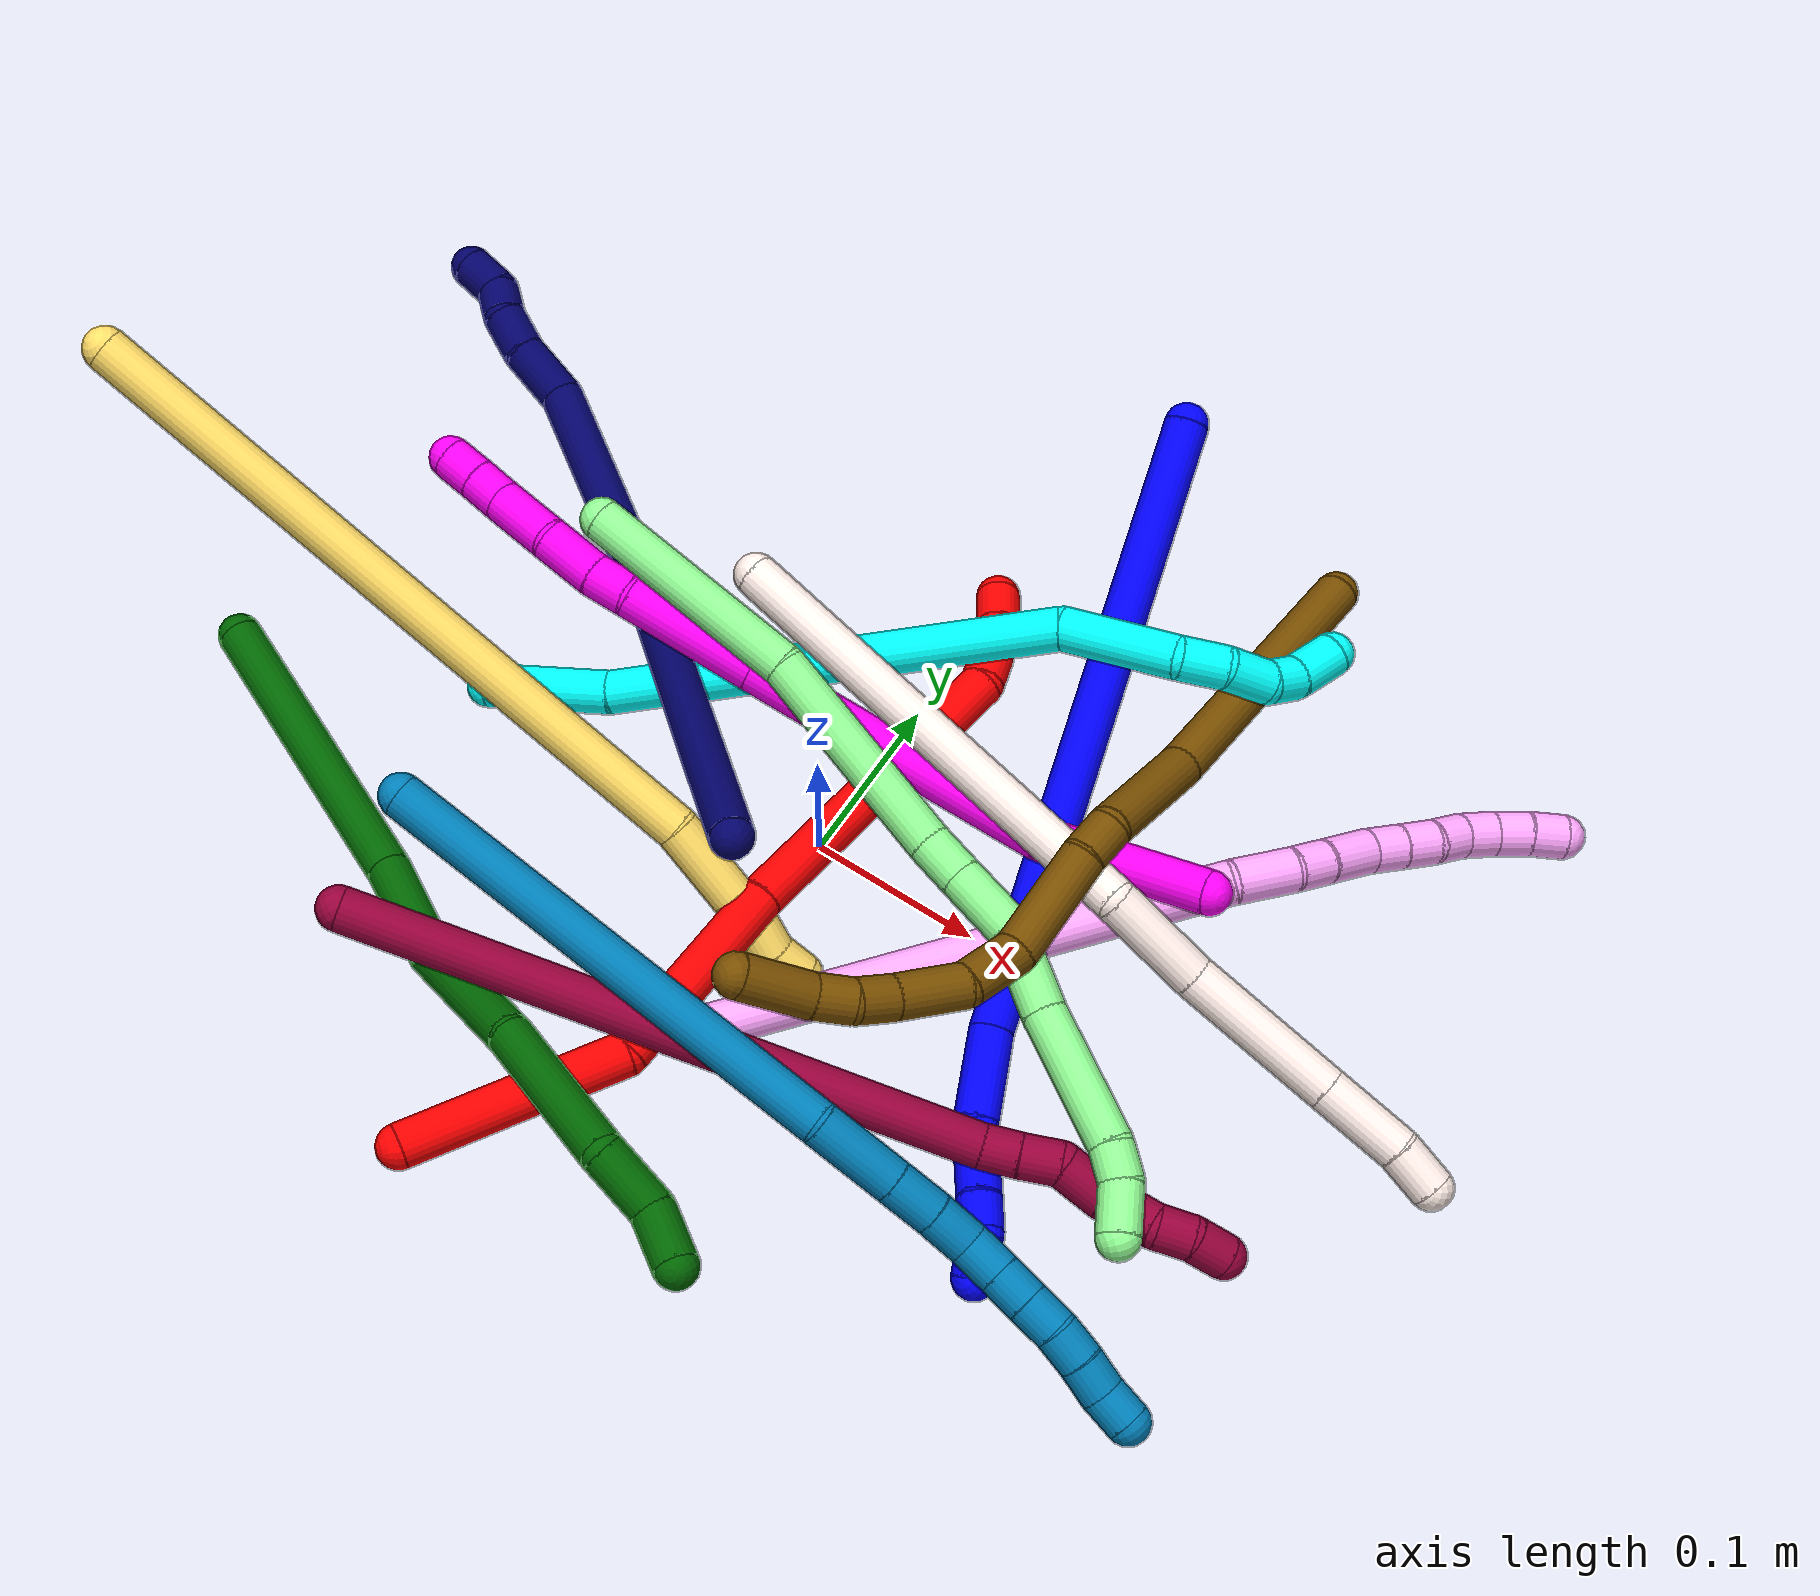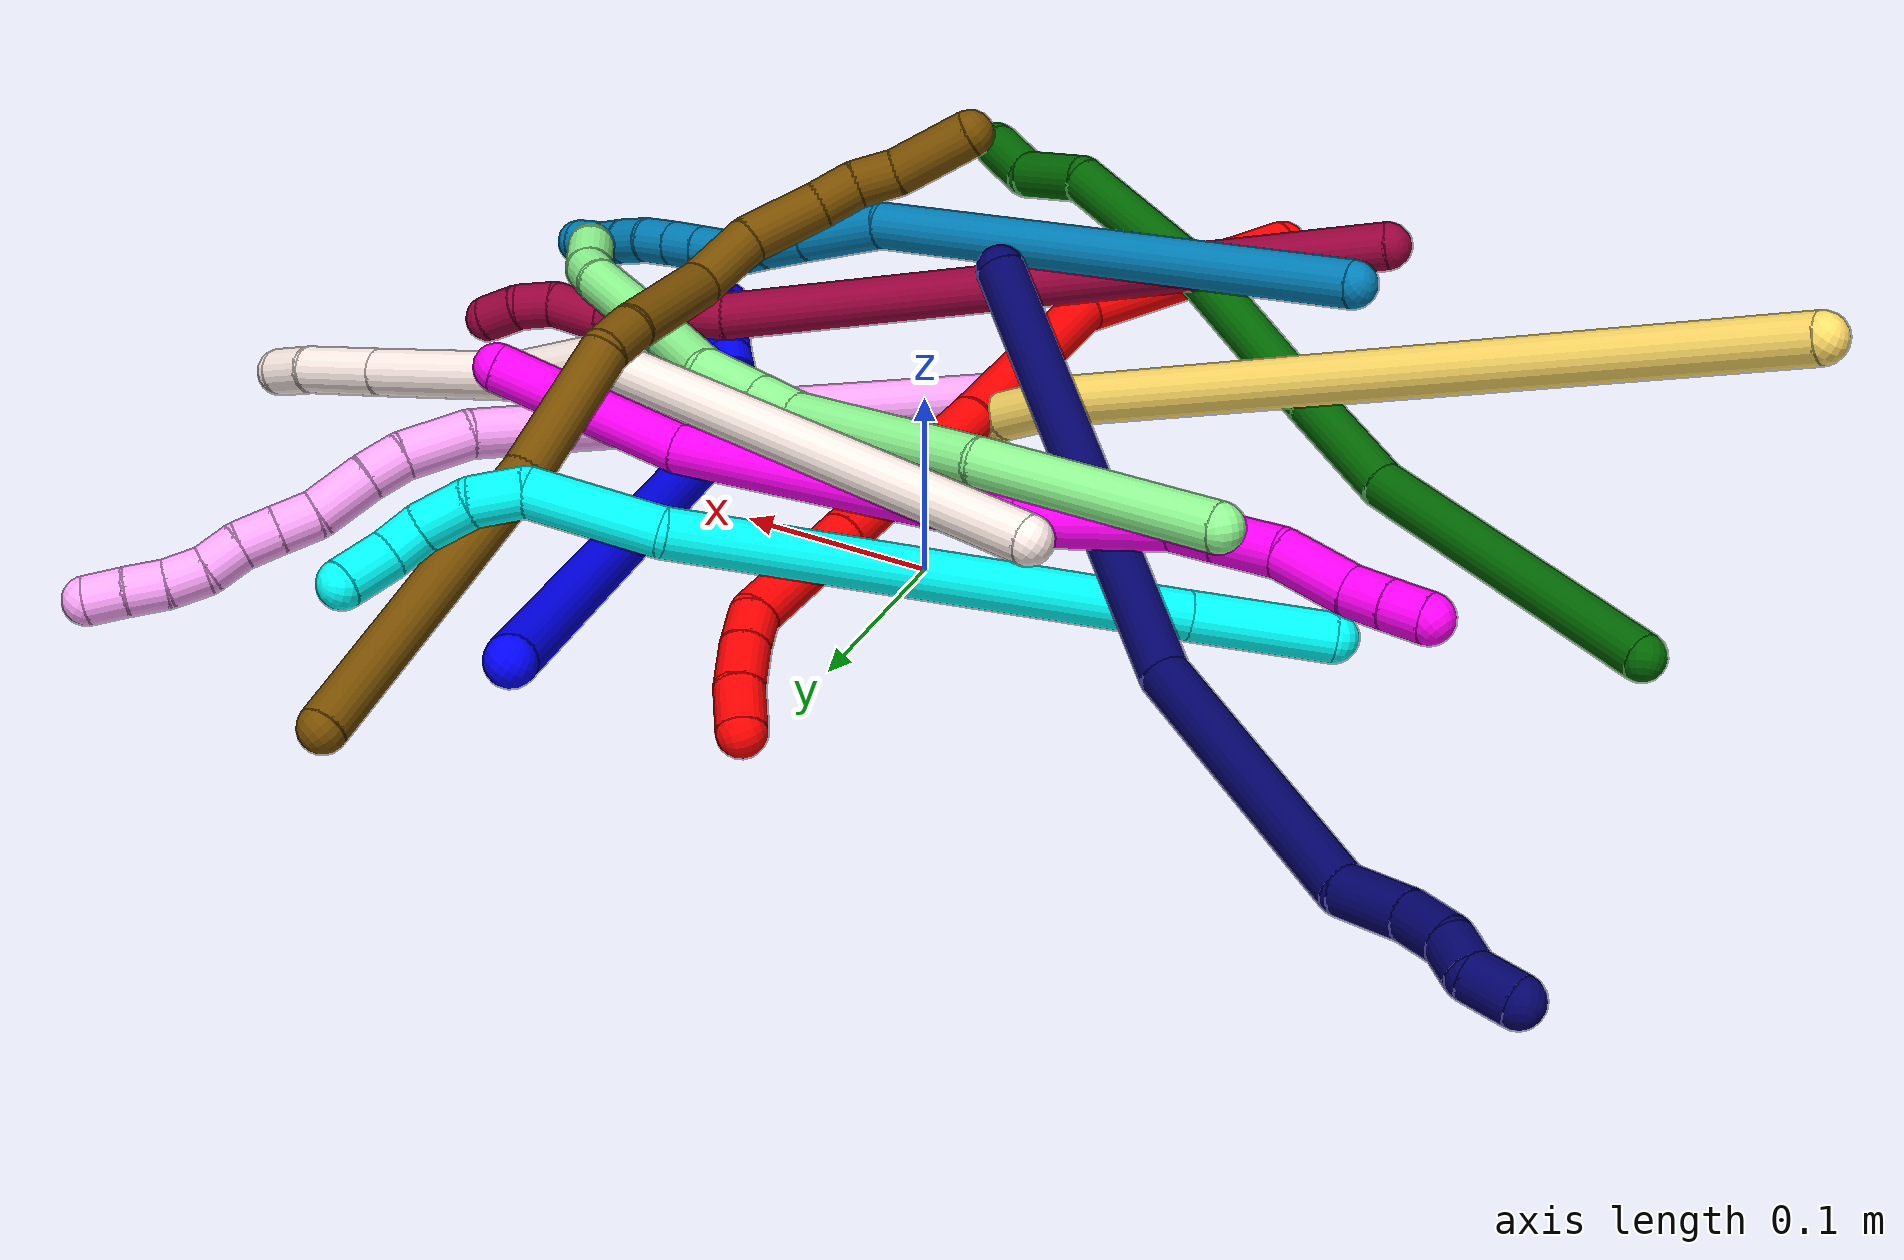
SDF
<sdf version="1.7">
 <world name="default">
  <plugin name="TubeGeneratorPlugin" filename="libtube_generator_plugin.so"/>
  <model name="photoneo_s_sensor">
   <static>1</static>
   <pose>0 0 2 1.57079 1.57079 3.14159</pose>
   <link name="link">
    <inertial><mass>0.1</mass></inertial>
    <sensor name="sensor" type="depth">
     <update_rate>30</update_rate>
     <camera>
      <horizontal_fov>1.22</horizontal_fov>
      <image><width>1920</width><height>1200</height><format>B8G8R8</format></image>
      <clip><near>0.1</near><far>4</far></clip>
      <depth_camera><output>points</output></depth_camera>
     </camera>
     <plugin name="camera_plugin" filename="libgazebo_ros_depth_camera.so">
      <baseline>0.2</baseline>
      <alwaysOn>1</alwaysOn>
      <updateRate>0.0</updateRate>
      <cameraName>camera_ir</cameraName>
      <imageTopicName>/camera/color/image_raw</imageTopicName>
      <cameraInfoTopicName>/camera/color/camera_info</cameraInfoTopicName>
      <depthImageTopicName>/camera/depth/image_raw</depthImageTopicName>
      <depthImageCameraInfoTopicName>/camera/depth/camera_info</depthImageCameraInfoTopicName>
      <pointCloudTopicName>/camera/depth/points</pointCloudTopicName>
      <frameName>fr_optical</frameName>
      <pointCloudCutoff>0.1</pointCloudCutoff>
      <pointCloudCutoffMax>2.0</pointCloudCutoffMax>
      <distortionK1>0</distortionK1>
      <distortionK2>0</distortionK2>
      <distortionK3>0</distortionK3>
      <distortionT1>0</distortionT1>
      <distortionT2>0</distortionT2>
      <CxPrime>0</CxPrime>
      <Cx>0</Cx>
      <Cy>0</Cy>
      <focalLength>0</focalLength>
      <hackBaseline>0</hackBaseline>
     </plugin>
    </sensor>
   </link>
  </model>
  <gravity>0 0 -9.8</gravity>
  <magnetic_field>6e-06 2.3e-05 -4.2e-05</magnetic_field>
  <atmosphere type="adiabatic"/>
  <physics name="default_physics" default="0" type="ode">
   <max_step_size>0.003</max_step_size>
   <real_time_factor>1</real_time_factor>
   <real_time_update_rate>1000</real_time_update_rate>
   <max_contacts>10000</max_contacts>
   <ode>
    <solver>
     <type>quick</type>
     <iters>100</iters>
     <sor>1.3</sor>
     <use_dynamic_moi_rescaling>0</use_dynamic_moi_rescaling>
    </solver>
    <constraints>
     <contact_max_correcting_vel>0</contact_max_correcting_vel>
     <contact_surface_layer>0.001</contact_surface_layer>
     <cfm>0</cfm>
     <erp>0.2</erp>
    </constraints>
   </ode>
  </physics>
  <scene><ambient>0.4 0.4 0.4 1</ambient><background>0.7 0.7 0.7 1</background><shadows>0</shadows></scene>
  <audio><device>default</device></audio>
  <spherical_coordinates>
   <surface_model>EARTH_WGS84</surface_model>
   <latitude_deg>0</latitude_deg>
   <longitude_deg>0</longitude_deg>
   <elevation>0</elevation>
   <heading_deg>0</heading_deg>
  </spherical_coordinates>
  <model name="bin">
   <static>1</static>
   <link name="bottom">
    <collision name="collision-bottom">
     <pose>0 0 -0.01 0 -0 0</pose>
     <geometry><box><size>0.8 0.6 0.02</size></box></geometry>
     <surface>
      <friction><ode><mu>100</mu><mu2>100</mu2></ode></friction>
      <contact><collide_bitmask>65535</collide_bitmask></contact>
     </surface>
    </collision>
   </link>
   <link name="west_wall">
    <collision name="collision-west_wall">
     <pose>-0.41 0 0.1 0 -0 0</pose>
     <geometry><box><size>0.02 0.6 0.2</size></box></geometry>
     <surface>
      <friction><ode><mu>100</mu><mu2>100</mu2></ode></friction>
      <contact><collide_bitmask>65535</collide_bitmask></contact>
     </surface>
    </collision>
   </link>
   <link name="east_wall">
    <collision name="collision-east_wall">
     <pose>0.41 0 0.1 0 -0 0</pose>
     <geometry><box><size>0.02 0.6 0.2</size></box></geometry>
     <surface>
      <friction><ode><mu>100</mu><mu2>100</mu2></ode></friction>
      <contact><collide_bitmask>65535</collide_bitmask></contact>
     </surface>
    </collision>
   </link>
   <link name="south_wall">
    <collision name="collision-south_wall">
     <pose>0 -0.31 0.1 0 -0 0</pose>
     <geometry><box><size>0.8 0.02 0.2</size></box></geometry>
     <surface>
      <friction><ode><mu>100</mu><mu2>100</mu2></ode></friction>
      <contact><collide_bitmask>65535</collide_bitmask></contact>
     </surface>
    </collision>
   </link>
   <link name="north_wall">
    <collision name="collision-north_wall">
     <pose>0 0.31 0.1 0 -0 0</pose>
     <geometry><box><size>0.8 0.02 0.2</size></box></geometry>
     <surface>
      <friction><ode><mu>100</mu><mu2>100</mu2></ode></friction>
      <contact><collide_bitmask>65535</collide_bitmask></contact>
     </surface>
    </collision>
   </link>
  </model>
  <model name="1">
   <static>0</static>
   <link name="1">
    <collision name="collision-cylinder-e_1_1_4">
     <pose>0.021454 -0.176658 0.013399 1.49509 0.120507 0.111732</pose>
     <geometry><cylinder><radius>0.0125</radius><length>0.35692</length></cylinder></geometry>
     <surface>
      <friction><ode><mu>1.16</mu><mu2>1.16</mu2><slip1>0</slip1><slip2>0</slip2></ode></friction>
      <contact><ode><kp>1e+06</kp><kd>1</kd><max_vel>0</max_vel><min_depth>0.001</min_depth></ode></contact>
     </surface>
    </collision>
    <visual name="visual-cylinder-e_1_1_4">
     <pose>0.021454 -0.176658 0.013399 1.49509 0.120507 0.111732</pose>
     <geometry><cylinder><radius>0.0125</radius><length>0.35692</length></cylinder></geometry>
     <material><ambient>0 0 1 1</ambient></material>
    </visual>
    <collision name="collision-cylinder-e_2_4_5">
     <pose>0.054496 -0.377655 0.034393 1.26837 0.426615 0.315985</pose>
     <geometry><cylinder><radius>0.0125</radius><length>0.056012</length></cylinder></geometry>
     <surface>
      <friction><ode><mu>1.16</mu><mu2>1.16</mu2><slip1>0</slip1><slip2>0</slip2></ode></friction>
      <contact><ode><kp>1e+06</kp><kd>1</kd><max_vel>0</max_vel><min_depth>0.001</min_depth></ode></contact>
     </surface>
    </collision>
    <visual name="visual-cylinder-e_2_4_5">
     <pose>0.054496 -0.377655 0.034393 1.26837 0.426615 0.315985</pose>
     <geometry><cylinder><radius>0.0125</radius><length>0.056012</length></cylinder></geometry>
     <material><ambient>0 0 1 1</ambient></material>
    </visual>
    <collision name="collision-cylinder-e_3_5_6">
     <pose>0.071962 -0.411629 0.042838 1.48263 0.546025 0.501884</pose>
     <geometry><cylinder><radius>0.0125</radius><length>0.022635</length></cylinder></geometry>
     <surface>
      <friction><ode><mu>1.16</mu><mu2>1.16</mu2><slip1>0</slip1><slip2>0</slip2></ode></friction>
      <contact><ode><kp>1e+06</kp><kd>1</kd><max_vel>0</max_vel><min_depth>0.001</min_depth></ode></contact>
     </surface>
    </collision>
    <visual name="visual-cylinder-e_3_5_6">
     <pose>0.071962 -0.411629 0.042838 1.48263 0.546025 0.501884</pose>
     <geometry><cylinder><radius>0.0125</radius><length>0.022635</length></cylinder></geometry>
     <material><ambient>0 0 1 1</ambient></material>
    </visual>
    <collision name="collision-cylinder-e_4_6_7">
     <pose>0.084239 -0.429139 0.046351 1.24488 0.656021 0.47903</pose>
     <geometry><cylinder><radius>0.0125</radius><length>0.020984</length></cylinder></geometry>
     <surface>
      <friction><ode><mu>1.16</mu><mu2>1.16</mu2><slip1>0</slip1><slip2>0</slip2></ode></friction>
      <contact><ode><kp>1e+06</kp><kd>1</kd><max_vel>0</max_vel><min_depth>0.001</min_depth></ode></contact>
     </surface>
    </collision>
    <visual name="visual-cylinder-e_4_6_7">
     <pose>0.084239 -0.429139 0.046351 1.24488 0.656021 0.47903</pose>
     <geometry><cylinder><radius>0.0125</radius><length>0.020984</length></cylinder></geometry>
     <material><ambient>0 0 1 1</ambient></material>
    </visual>
    <collision name="collision-cylinder-e_5_7_8">
     <pose>0.096273 -0.445211 0.050552 1.38517 0.594268 0.497574</pose>
     <geometry><cylinder><radius>0.0125</radius><length>0.020128</length></cylinder></geometry>
     <surface>
      <friction><ode><mu>1.16</mu><mu2>1.16</mu2><slip1>0</slip1><slip2>0</slip2></ode></friction>
      <contact><ode><kp>1e+06</kp><kd>1</kd><max_vel>0</max_vel><min_depth>0.001</min_depth></ode></contact>
     </surface>
    </collision>
    <visual name="visual-cylinder-e_5_7_8">
     <pose>0.096273 -0.445211 0.050552 1.38517 0.594268 0.497574</pose>
     <geometry><cylinder><radius>0.0125</radius><length>0.020128</length></cylinder></geometry>
     <material><ambient>0 0 1 1</ambient></material>
    </visual>
    <collision name="collision-cylinder-e_6_8_2">
     <pose>0.104071 -0.464807 0.05094 1.67141 0.186524 0.20617</pose>
     <geometry><cylinder><radius>0.0125</radius><length>0.023321</length></cylinder></geometry>
     <surface>
      <friction><ode><mu>1.16</mu><mu2>1.16</mu2><slip1>0</slip1><slip2>0</slip2></ode></friction>
      <contact><ode><kp>1e+06</kp><kd>1</kd><max_vel>0</max_vel><min_depth>0.001</min_depth></ode></contact>
     </surface>
    </collision>
    <visual name="visual-cylinder-e_6_8_2">
     <pose>0.104071 -0.464807 0.05094 1.67141 0.186524 0.20617</pose>
     <geometry><cylinder><radius>0.0125</radius><length>0.023321</length></cylinder></geometry>
     <material><ambient>0 0 1 1</ambient></material>
    </visual>
    <collision name="collision-sphere-2">
     <pose>0.106233 -0.476207 0.04979 0 -0 0</pose>
     <geometry><sphere><radius>0.0125</radius></sphere></geometry>
     <surface>
      <friction><ode><mu>1.16</mu><mu2>1.16</mu2><slip1>0</slip1><slip2>0</slip2></ode></friction>
      <contact><ode><kp>1e+06</kp><kd>1</kd><max_vel>0</max_vel><min_depth>0.001</min_depth></ode></contact>
     </surface>
    </collision>
    <visual name="visual-sphere-2">
     <pose>0.106233 -0.476207 0.04979 0 -0 0</pose>
     <geometry><sphere><radius>0.0125</radius></sphere></geometry>
     <material><ambient>0 0 1 1</ambient></material>
    </visual>
    <collision name="collision-sphere-4">
     <pose>0.042907 -0.353316 0.026799 0 -0 0</pose>
     <geometry><sphere><radius>0.0125</radius></sphere></geometry>
     <surface>
      <friction><ode><mu>1.16</mu><mu2>1.16</mu2><slip1>0</slip1><slip2>0</slip2></ode></friction>
      <contact><ode><kp>1e+06</kp><kd>1</kd><max_vel>0</max_vel><min_depth>0.001</min_depth></ode></contact>
     </surface>
    </collision>
    <visual name="visual-sphere-4">
     <pose>0.042907 -0.353316 0.026799 0 -0 0</pose>
     <geometry><sphere><radius>0.0125</radius></sphere></geometry>
     <material><ambient>0 0 1 1</ambient></material>
    </visual>
    <collision name="collision-sphere-1">
     <geometry><sphere><radius>0.0125</radius></sphere></geometry>
     <surface>
      <friction><ode><mu>1.16</mu><mu2>1.16</mu2><slip1>0</slip1><slip2>0</slip2></ode></friction>
      <contact><ode><kp>1e+06</kp><kd>1</kd><max_vel>0</max_vel><min_depth>0.001</min_depth></ode></contact>
     </surface>
    </collision>
    <visual name="visual-sphere-1">
     <geometry><sphere><radius>0.0125</radius></sphere></geometry>
     <material><ambient>0 0 1 1</ambient></material>
    </visual>
    <collision name="collision-sphere-8">
     <pose>0.101908 -0.453406 0.052091 0 -0 0</pose>
     <geometry><sphere><radius>0.0125</radius></sphere></geometry>
     <surface>
      <friction><ode><mu>1.16</mu><mu2>1.16</mu2><slip1>0</slip1><slip2>0</slip2></ode></friction>
      <contact><ode><kp>1e+06</kp><kd>1</kd><max_vel>0</max_vel><min_depth>0.001</min_depth></ode></contact>
     </surface>
    </collision>
    <visual name="visual-sphere-8">
     <pose>0.101908 -0.453406 0.052091 0 -0 0</pose>
     <geometry><sphere><radius>0.0125</radius></sphere></geometry>
     <material><ambient>0 0 1 1</ambient></material>
    </visual>
    <collision name="collision-sphere-5">
     <pose>0.066085 -0.401994 0.041986 0 -0 0</pose>
     <geometry><sphere><radius>0.0125</radius></sphere></geometry>
     <surface>
      <friction><ode><mu>1.16</mu><mu2>1.16</mu2><slip1>0</slip1><slip2>0</slip2></ode></friction>
      <contact><ode><kp>1e+06</kp><kd>1</kd><max_vel>0</max_vel><min_depth>0.001</min_depth></ode></contact>
     </surface>
    </collision>
    <visual name="visual-sphere-5">
     <pose>0.066085 -0.401994 0.041986 0 -0 0</pose>
     <geometry><sphere><radius>0.0125</radius></sphere></geometry>
     <material><ambient>0 0 1 1</ambient></material>
    </visual>
    <collision name="collision-sphere-6">
     <pose>0.077839 -0.421263 0.04369 0 -0 0</pose>
     <geometry><sphere><radius>0.0125</radius></sphere></geometry>
     <surface>
      <friction><ode><mu>1.16</mu><mu2>1.16</mu2><slip1>0</slip1><slip2>0</slip2></ode></friction>
      <contact><ode><kp>1e+06</kp><kd>1</kd><max_vel>0</max_vel><min_depth>0.001</min_depth></ode></contact>
     </surface>
    </collision>
    <visual name="visual-sphere-6">
     <pose>0.077839 -0.421263 0.04369 0 -0 0</pose>
     <geometry><sphere><radius>0.0125</radius></sphere></geometry>
     <material><ambient>0 0 1 1</ambient></material>
    </visual>
    <collision name="collision-sphere-7">
     <pose>0.090638 -0.437016 0.049013 0 -0 0</pose>
     <geometry><sphere><radius>0.0125</radius></sphere></geometry>
     <surface>
      <friction><ode><mu>1.16</mu><mu2>1.16</mu2><slip1>0</slip1><slip2>0</slip2></ode></friction>
      <contact><ode><kp>1e+06</kp><kd>1</kd><max_vel>0</max_vel><min_depth>0.001</min_depth></ode></contact>
     </surface>
    </collision>
    <visual name="visual-sphere-7">
     <pose>0.090638 -0.437016 0.049013 0 -0 0</pose>
     <geometry><sphere><radius>0.0125</radius></sphere></geometry>
     <material><ambient>0 0 1 1</ambient></material>
    </visual>
    <inertial>
     <pose>0.036942 -0.244659 0.021713 0 -0 0</pose>
     <mass>0.5</mass>
     <inertia>
      <ixx>0.004208</ixx>
      <ixy>0</ixy>
      <ixz>0</ixz>
      <iyy>0.000736</iyy>
      <iyz>0</iyz>
      <izz>0.003322</izz>
     </inertia>
    </inertial>
   </link>
   <pose>0.054432 0.287639 0.106319 0.447075 -0.473723 -0.028666</pose>
  </model>
  <model name="2">
   <static>0</static>
   <link name="2">
    <collision name="collision-cylinder-e_1_1_4">
     <pose>0.009427 0.008392 -0.062593 -3.00832 0.148171 -1.6769</pose>
     <geometry><cylinder><radius>0.0125</radius><length>0.127705</length></cylinder></geometry>
     <surface>
      <friction><ode><mu>1.16</mu><mu2>1.16</mu2><slip1>0</slip1><slip2>0</slip2></ode></friction>
      <contact><ode><kp>1e+06</kp><kd>1</kd><max_vel>0</max_vel><min_depth>0.001</min_depth></ode></contact>
     </surface>
    </collision>
    <visual name="visual-cylinder-e_1_1_4">
     <pose>0.009427 0.008392 -0.062593 -3.00832 0.148171 -1.6769</pose>
     <geometry><cylinder><radius>0.0125</radius><length>0.127705</length></cylinder></geometry>
     <material><ambient>1 0 0 1</ambient></material>
    </visual>
    <collision name="collision-cylinder-e_2_4_5">
     <pose>0.023382 0.050844 -0.171923 -2.51183 0.078157 -0.238931</pose>
     <geometry><cylinder><radius>0.0125</radius><length>0.116016</length></cylinder></geometry>
     <surface>
      <friction><ode><mu>1.16</mu><mu2>1.16</mu2><slip1>0</slip1><slip2>0</slip2></ode></friction>
      <contact><ode><kp>1e+06</kp><kd>1</kd><max_vel>0</max_vel><min_depth>0.001</min_depth></ode></contact>
     </surface>
    </collision>
    <visual name="visual-cylinder-e_2_4_5">
     <pose>0.023382 0.050844 -0.171923 -2.51183 0.078157 -0.238931</pose>
     <geometry><cylinder><radius>0.0125</radius><length>0.116016</length></cylinder></geometry>
     <material><ambient>1 0 0 1</ambient></material>
    </visual>
    <collision name="collision-cylinder-e_3_5_6">
     <pose>0.030295 0.11444 -0.26682 -2.59145 0.042173 -0.149177</pose>
     <geometry><cylinder><radius>0.0125</radius><length>0.113092</length></cylinder></geometry>
     <surface>
      <friction><ode><mu>1.16</mu><mu2>1.16</mu2><slip1>0</slip1><slip2>0</slip2></ode></friction>
      <contact><ode><kp>1e+06</kp><kd>1</kd><max_vel>0</max_vel><min_depth>0.001</min_depth></ode></contact>
     </surface>
    </collision>
    <visual name="visual-cylinder-e_3_5_6">
     <pose>0.030295 0.11444 -0.26682 -2.59145 0.042173 -0.149177</pose>
     <geometry><cylinder><radius>0.0125</radius><length>0.113092</length></cylinder></geometry>
     <material><ambient>1 0 0 1</ambient></material>
    </visual>
    <collision name="collision-cylinder-e_4_6_7">
     <pose>0.034171 0.162978 -0.345756 -2.58846 0.041204 -0.144932</pose>
     <geometry><cylinder><radius>0.0125</radius><length>0.0724</length></cylinder></geometry>
     <surface>
      <friction><ode><mu>1.16</mu><mu2>1.16</mu2><slip1>0</slip1><slip2>0</slip2></ode></friction>
      <contact><ode><kp>1e+06</kp><kd>1</kd><max_vel>0</max_vel><min_depth>0.001</min_depth></ode></contact>
     </surface>
    </collision>
    <visual name="visual-cylinder-e_4_6_7">
     <pose>0.034171 0.162978 -0.345756 -2.58846 0.041204 -0.144932</pose>
     <geometry><cylinder><radius>0.0125</radius><length>0.0724</length></cylinder></geometry>
     <material><ambient>1 0 0 1</ambient></material>
    </visual>
    <collision name="collision-cylinder-e_5_7_8">
     <pose>0.033943 0.190082 -0.382383 -2.19621 -0.170332 0.330856</pose>
     <geometry><cylinder><radius>0.0125</radius><length>0.020282</length></cylinder></geometry>
     <surface>
      <friction><ode><mu>1.16</mu><mu2>1.16</mu2><slip1>0</slip1><slip2>0</slip2></ode></friction>
      <contact><ode><kp>1e+06</kp><kd>1</kd><max_vel>0</max_vel><min_depth>0.001</min_depth></ode></contact>
     </surface>
    </collision>
    <visual name="visual-cylinder-e_5_7_8">
     <pose>0.033943 0.190082 -0.382383 -2.19621 -0.170332 0.330856</pose>
     <geometry><cylinder><radius>0.0125</radius><length>0.020282</length></cylinder></geometry>
     <material><ambient>1 0 0 1</ambient></material>
    </visual>
    <collision name="collision-cylinder-e_6_8_9">
     <pose>0.029641 0.208846 -0.394522 -2.10367 -0.20573 0.357597</pose>
     <geometry><cylinder><radius>0.0125</radius><length>0.025289</length></cylinder></geometry>
     <surface>
      <friction><ode><mu>1.16</mu><mu2>1.16</mu2><slip1>0</slip1><slip2>0</slip2></ode></friction>
      <contact><ode><kp>1e+06</kp><kd>1</kd><max_vel>0</max_vel><min_depth>0.001</min_depth></ode></contact>
     </surface>
    </collision>
    <visual name="visual-cylinder-e_6_8_9">
     <pose>0.029641 0.208846 -0.394522 -2.10367 -0.20573 0.357597</pose>
     <geometry><cylinder><radius>0.0125</radius><length>0.025289</length></cylinder></geometry>
     <material><ambient>1 0 0 1</ambient></material>
    </visual>
    <collision name="collision-cylinder-e_7_9_2">
     <pose>0.023467 0.230712 -0.405341 -1.95513 -0.288838 0.424882</pose>
     <geometry><cylinder><radius>0.0125</radius><length>0.025215</length></cylinder></geometry>
     <surface>
      <friction><ode><mu>1.16</mu><mu2>1.16</mu2><slip1>0</slip1><slip2>0</slip2></ode></friction>
      <contact><ode><kp>1e+06</kp><kd>1</kd><max_vel>0</max_vel><min_depth>0.001</min_depth></ode></contact>
     </surface>
    </collision>
    <visual name="visual-cylinder-e_7_9_2">
     <pose>0.023467 0.230712 -0.405341 -1.95513 -0.288838 0.424882</pose>
     <geometry><cylinder><radius>0.0125</radius><length>0.025215</length></cylinder></geometry>
     <material><ambient>1 0 0 1</ambient></material>
    </visual>
    <collision name="collision-sphere-2">
     <pose>0.019875 0.241915 -0.409872 0 -0 0</pose>
     <geometry><sphere><radius>0.0125</radius></sphere></geometry>
     <surface>
      <friction><ode><mu>1.16</mu><mu2>1.16</mu2><slip1>0</slip1><slip2>0</slip2></ode></friction>
      <contact><ode><kp>1e+06</kp><kd>1</kd><max_vel>0</max_vel><min_depth>0.001</min_depth></ode></contact>
     </surface>
    </collision>
    <visual name="visual-sphere-2">
     <pose>0.019875 0.241915 -0.409872 0 -0 0</pose>
     <geometry><sphere><radius>0.0125</radius></sphere></geometry>
     <material><ambient>1 0 0 1</ambient></material>
    </visual>
    <collision name="collision-sphere-9">
     <pose>0.027058 0.219508 -0.40081 0 -0 0</pose>
     <geometry><sphere><radius>0.0125</radius></sphere></geometry>
     <surface>
      <friction><ode><mu>1.16</mu><mu2>1.16</mu2><slip1>0</slip1><slip2>0</slip2></ode></friction>
      <contact><ode><kp>1e+06</kp><kd>1</kd><max_vel>0</max_vel><min_depth>0.001</min_depth></ode></contact>
     </surface>
    </collision>
    <visual name="visual-sphere-9">
     <pose>0.027058 0.219508 -0.40081 0 -0 0</pose>
     <geometry><sphere><radius>0.0125</radius></sphere></geometry>
     <material><ambient>1 0 0 1</ambient></material>
    </visual>
    <collision name="collision-sphere-4">
     <pose>0.018853 0.016784 -0.125186 0 -0 0</pose>
     <geometry><sphere><radius>0.0125</radius></sphere></geometry>
     <surface>
      <friction><ode><mu>1.16</mu><mu2>1.16</mu2><slip1>0</slip1><slip2>0</slip2></ode></friction>
      <contact><ode><kp>1e+06</kp><kd>1</kd><max_vel>0</max_vel><min_depth>0.001</min_depth></ode></contact>
     </surface>
    </collision>
    <visual name="visual-sphere-4">
     <pose>0.018853 0.016784 -0.125186 0 -0 0</pose>
     <geometry><sphere><radius>0.0125</radius></sphere></geometry>
     <material><ambient>1 0 0 1</ambient></material>
    </visual>
    <collision name="collision-sphere-1">
     <geometry><sphere><radius>0.0125</radius></sphere></geometry>
     <surface>
      <friction><ode><mu>1.16</mu><mu2>1.16</mu2><slip1>0</slip1><slip2>0</slip2></ode></friction>
      <contact><ode><kp>1e+06</kp><kd>1</kd><max_vel>0</max_vel><min_depth>0.001</min_depth></ode></contact>
     </surface>
    </collision>
    <visual name="visual-sphere-1">
     <geometry><sphere><radius>0.0125</radius></sphere></geometry>
     <material><ambient>1 0 0 1</ambient></material>
    </visual>
    <collision name="collision-sphere-8">
     <pose>0.032224 0.198185 -0.388234 0 -0 0</pose>
     <geometry><sphere><radius>0.0125</radius></sphere></geometry>
     <surface>
      <friction><ode><mu>1.16</mu><mu2>1.16</mu2><slip1>0</slip1><slip2>0</slip2></ode></friction>
      <contact><ode><kp>1e+06</kp><kd>1</kd><max_vel>0</max_vel><min_depth>0.001</min_depth></ode></contact>
     </surface>
    </collision>
    <visual name="visual-sphere-8">
     <pose>0.032224 0.198185 -0.388234 0 -0 0</pose>
     <geometry><sphere><radius>0.0125</radius></sphere></geometry>
     <material><ambient>1 0 0 1</ambient></material>
    </visual>
    <collision name="collision-sphere-5">
     <pose>0.027911 0.084903 -0.21866 0 -0 0</pose>
     <geometry><sphere><radius>0.0125</radius></sphere></geometry>
     <surface>
      <friction><ode><mu>1.16</mu><mu2>1.16</mu2><slip1>0</slip1><slip2>0</slip2></ode></friction>
      <contact><ode><kp>1e+06</kp><kd>1</kd><max_vel>0</max_vel><min_depth>0.001</min_depth></ode></contact>
     </surface>
    </collision>
    <visual name="visual-sphere-5">
     <pose>0.027911 0.084903 -0.21866 0 -0 0</pose>
     <geometry><sphere><radius>0.0125</radius></sphere></geometry>
     <material><ambient>1 0 0 1</ambient></material>
    </visual>
    <collision name="collision-sphere-6">
     <pose>0.032679 0.143976 -0.31498 0 -0 0</pose>
     <geometry><sphere><radius>0.0125</radius></sphere></geometry>
     <surface>
      <friction><ode><mu>1.16</mu><mu2>1.16</mu2><slip1>0</slip1><slip2>0</slip2></ode></friction>
      <contact><ode><kp>1e+06</kp><kd>1</kd><max_vel>0</max_vel><min_depth>0.001</min_depth></ode></contact>
     </surface>
    </collision>
    <visual name="visual-sphere-6">
     <pose>0.032679 0.143976 -0.31498 0 -0 0</pose>
     <geometry><sphere><radius>0.0125</radius></sphere></geometry>
     <material><ambient>1 0 0 1</ambient></material>
    </visual>
    <collision name="collision-sphere-7">
     <pose>0.035662 0.18198 -0.376532 0 -0 0</pose>
     <geometry><sphere><radius>0.0125</radius></sphere></geometry>
     <surface>
      <friction><ode><mu>1.16</mu><mu2>1.16</mu2><slip1>0</slip1><slip2>0</slip2></ode></friction>
      <contact><ode><kp>1e+06</kp><kd>1</kd><max_vel>0</max_vel><min_depth>0.001</min_depth></ode></contact>
     </surface>
    </collision>
    <visual name="visual-sphere-7">
     <pose>0.035662 0.18198 -0.376532 0 -0 0</pose>
     <geometry><sphere><radius>0.0125</radius></sphere></geometry>
     <material><ambient>1 0 0 1</ambient></material>
    </visual>
    <inertial>
     <pose>0.023693 0.093333 -0.222201 0 -0 0</pose>
     <mass>0.5</mass>
     <inertia>
      <ixx>4.8e-05</ixx>
      <ixy>0</ixy>
      <ixz>0</ixz>
      <iyy>-0.000428</iyy>
      <iyz>0</iyz>
      <izz>-0.000265</izz>
     </inertia>
    </inertial>
   </link>
   <pose>-0.068901 -0.287499 0.061838 0.213977 -1.38481 0.671209</pose>
  </model>
  <model name="3">
   <static>0</static>
   <link name="3">
    <collision name="collision-cylinder-e_1_1_4">
     <pose>0.004084 -0.018199 0.030387 0.539609 0.114785 0.031776</pose>
     <geometry><cylinder><radius>0.0125</radius><length>0.071309</length></cylinder></geometry>
     <surface>
      <friction><ode><mu>1.16</mu><mu2>1.16</mu2><slip1>0</slip1><slip2>0</slip2></ode></friction>
      <contact><ode><kp>1e+06</kp><kd>1</kd><max_vel>0</max_vel><min_depth>0.001</min_depth></ode></contact>
     </surface>
    </collision>
    <visual name="visual-cylinder-e_1_1_4">
     <pose>0.004084 -0.018199 0.030387 0.539609 0.114785 0.031776</pose>
     <geometry><cylinder><radius>0.0125</radius><length>0.071309</length></cylinder></geometry>
     <material><ambient>0.003922 1 0.996078 1</ambient></material>
    </visual>
    <collision name="collision-cylinder-e_2_4_5">
     <pose>0.012272 -0.082649 0.181919 0.364709 0.031642 0.005835</pose>
     <geometry><cylinder><radius>0.0125</radius><length>0.259477</length></cylinder></geometry>
     <surface>
      <friction><ode><mu>1.16</mu><mu2>1.16</mu2><slip1>0</slip1><slip2>0</slip2></ode></friction>
      <contact><ode><kp>1e+06</kp><kd>1</kd><max_vel>0</max_vel><min_depth>0.001</min_depth></ode></contact>
     </surface>
    </collision>
    <visual name="visual-cylinder-e_2_4_5">
     <pose>0.012272 -0.082649 0.181919 0.364709 0.031642 0.005835</pose>
     <geometry><cylinder><radius>0.0125</radius><length>0.259477</length></cylinder></geometry>
     <material><ambient>0.003922 1 0.996078 1</ambient></material>
    </visual>
    <collision name="collision-cylinder-e_3_5_6">
     <pose>0.018221 -0.151836 0.32734 0.75698 0.055176 0.021946</pose>
     <geometry><cylinder><radius>0.0125</radius><length>0.066895</length></cylinder></geometry>
     <surface>
      <friction><ode><mu>1.16</mu><mu2>1.16</mu2><slip1>0</slip1><slip2>0</slip2></ode></friction>
      <contact><ode><kp>1e+06</kp><kd>1</kd><max_vel>0</max_vel><min_depth>0.001</min_depth></ode></contact>
     </surface>
    </collision>
    <visual name="visual-cylinder-e_3_5_6">
     <pose>0.018221 -0.151836 0.32734 0.75698 0.055176 0.021946</pose>
     <geometry><cylinder><radius>0.0125</radius><length>0.066895</length></cylinder></geometry>
     <material><ambient>0.003922 1 0.996078 1</ambient></material>
    </visual>
    <collision name="collision-cylinder-e_4_6_7">
     <pose>0.026307 -0.18122 0.361515 0.577515 0.486021 0.147023</pose>
     <geometry><cylinder><radius>0.0125</radius><length>0.026725</length></cylinder></geometry>
     <surface>
      <friction><ode><mu>1.16</mu><mu2>1.16</mu2><slip1>0</slip1><slip2>0</slip2></ode></friction>
      <contact><ode><kp>1e+06</kp><kd>1</kd><max_vel>0</max_vel><min_depth>0.001</min_depth></ode></contact>
     </surface>
    </collision>
    <visual name="visual-cylinder-e_4_6_7">
     <pose>0.026307 -0.18122 0.361515 0.577515 0.486021 0.147023</pose>
     <geometry><cylinder><radius>0.0125</radius><length>0.026725</length></cylinder></geometry>
     <material><ambient>0.003922 1 0.996078 1</ambient></material>
    </visual>
    <collision name="collision-cylinder-e_5_7_8">
     <pose>0.042406 -0.193147 0.379512 0.594579 0.789542 0.25392</pose>
     <geometry><cylinder><radius>0.0125</radius><length>0.027766</length></cylinder></geometry>
     <surface>
      <friction><ode><mu>1.16</mu><mu2>1.16</mu2><slip1>0</slip1><slip2>0</slip2></ode></friction>
      <contact><ode><kp>1e+06</kp><kd>1</kd><max_vel>0</max_vel><min_depth>0.001</min_depth></ode></contact>
     </surface>
    </collision>
    <visual name="visual-cylinder-e_5_7_8">
     <pose>0.042406 -0.193147 0.379512 0.594579 0.789542 0.25392</pose>
     <geometry><cylinder><radius>0.0125</radius><length>0.027766</length></cylinder></geometry>
     <material><ambient>0.003922 1 0.996078 1</ambient></material>
    </visual>
    <collision name="collision-cylinder-e_6_8_9">
     <pose>0.059326 -0.198285 0.394842 -0.046708 0.77303 -0.019013</pose>
     <geometry><cylinder><radius>0.0125</radius><length>0.020228</length></cylinder></geometry>
     <surface>
      <friction><ode><mu>1.16</mu><mu2>1.16</mu2><slip1>0</slip1><slip2>0</slip2></ode></friction>
      <contact><ode><kp>1e+06</kp><kd>1</kd><max_vel>0</max_vel><min_depth>0.001</min_depth></ode></contact>
     </surface>
    </collision>
    <visual name="visual-cylinder-e_6_8_9">
     <pose>0.059326 -0.198285 0.394842 -0.046708 0.77303 -0.019013</pose>
     <geometry><cylinder><radius>0.0125</radius><length>0.020228</length></cylinder></geometry>
     <material><ambient>0.003922 1 0.996078 1</ambient></material>
    </visual>
    <collision name="collision-cylinder-e_7_9_2">
     <pose>0.072474 -0.194462 0.413959 -0.285214 0.4567 -0.066713</pose>
     <geometry><cylinder><radius>0.0125</radius><length>0.0276</length></cylinder></geometry>
     <surface>
      <friction><ode><mu>1.16</mu><mu2>1.16</mu2><slip1>0</slip1><slip2>0</slip2></ode></friction>
      <contact><ode><kp>1e+06</kp><kd>1</kd><max_vel>0</max_vel><min_depth>0.001</min_depth></ode></contact>
     </surface>
    </collision>
    <visual name="visual-cylinder-e_7_9_2">
     <pose>0.072474 -0.194462 0.413959 -0.285214 0.4567 -0.066713</pose>
     <geometry><cylinder><radius>0.0125</radius><length>0.0276</length></cylinder></geometry>
     <material><ambient>0.003922 1 0.996078 1</ambient></material>
    </visual>
    <collision name="collision-sphere-2">
     <pose>0.07856 -0.190977 0.425845 0 -0 0</pose>
     <geometry><sphere><radius>0.0125</radius></sphere></geometry>
     <surface>
      <friction><ode><mu>1.16</mu><mu2>1.16</mu2><slip1>0</slip1><slip2>0</slip2></ode></friction>
      <contact><ode><kp>1e+06</kp><kd>1</kd><max_vel>0</max_vel><min_depth>0.001</min_depth></ode></contact>
     </surface>
    </collision>
    <visual name="visual-sphere-2">
     <pose>0.07856 -0.190977 0.425845 0 -0 0</pose>
     <geometry><sphere><radius>0.0125</radius></sphere></geometry>
     <material><ambient>0.003922 1 0.996078 1</ambient></material>
    </visual>
    <collision name="collision-sphere-9">
     <pose>0.066389 -0.197947 0.402074 0 -0 0</pose>
     <geometry><sphere><radius>0.0125</radius></sphere></geometry>
     <surface>
      <friction><ode><mu>1.16</mu><mu2>1.16</mu2><slip1>0</slip1><slip2>0</slip2></ode></friction>
      <contact><ode><kp>1e+06</kp><kd>1</kd><max_vel>0</max_vel><min_depth>0.001</min_depth></ode></contact>
     </surface>
    </collision>
    <visual name="visual-sphere-9">
     <pose>0.066389 -0.197947 0.402074 0 -0 0</pose>
     <geometry><sphere><radius>0.0125</radius></sphere></geometry>
     <material><ambient>0.003922 1 0.996078 1</ambient></material>
    </visual>
    <collision name="collision-sphere-4">
     <pose>0.008167 -0.036398 0.060775 0 -0 0</pose>
     <geometry><sphere><radius>0.0125</radius></sphere></geometry>
     <surface>
      <friction><ode><mu>1.16</mu><mu2>1.16</mu2><slip1>0</slip1><slip2>0</slip2></ode></friction>
      <contact><ode><kp>1e+06</kp><kd>1</kd><max_vel>0</max_vel><min_depth>0.001</min_depth></ode></contact>
     </surface>
    </collision>
    <visual name="visual-sphere-4">
     <pose>0.008167 -0.036398 0.060775 0 -0 0</pose>
     <geometry><sphere><radius>0.0125</radius></sphere></geometry>
     <material><ambient>0.003922 1 0.996078 1</ambient></material>
    </visual>
    <collision name="collision-sphere-1">
     <geometry><sphere><radius>0.0125</radius></sphere></geometry>
     <surface>
      <friction><ode><mu>1.16</mu><mu2>1.16</mu2><slip1>0</slip1><slip2>0</slip2></ode></friction>
      <contact><ode><kp>1e+06</kp><kd>1</kd><max_vel>0</max_vel><min_depth>0.001</min_depth></ode></contact>
     </surface>
    </collision>
    <visual name="visual-sphere-1">
     <geometry><sphere><radius>0.0125</radius></sphere></geometry>
     <material><ambient>0.003922 1 0.996078 1</ambient></material>
    </visual>
    <collision name="collision-sphere-8">
     <pose>0.052263 -0.198623 0.387611 0 -0 0</pose>
     <geometry><sphere><radius>0.0125</radius></sphere></geometry>
     <surface>
      <friction><ode><mu>1.16</mu><mu2>1.16</mu2><slip1>0</slip1><slip2>0</slip2></ode></friction>
      <contact><ode><kp>1e+06</kp><kd>1</kd><max_vel>0</max_vel><min_depth>0.001</min_depth></ode></contact>
     </surface>
    </collision>
    <visual name="visual-sphere-8">
     <pose>0.052263 -0.198623 0.387611 0 -0 0</pose>
     <geometry><sphere><radius>0.0125</radius></sphere></geometry>
     <material><ambient>0.003922 1 0.996078 1</ambient></material>
    </visual>
    <collision name="collision-sphere-5">
     <pose>0.016376 -0.128901 0.303063 0 -0 0</pose>
     <geometry><sphere><radius>0.0125</radius></sphere></geometry>
     <surface>
      <friction><ode><mu>1.16</mu><mu2>1.16</mu2><slip1>0</slip1><slip2>0</slip2></ode></friction>
      <contact><ode><kp>1e+06</kp><kd>1</kd><max_vel>0</max_vel><min_depth>0.001</min_depth></ode></contact>
     </surface>
    </collision>
    <visual name="visual-sphere-5">
     <pose>0.016376 -0.128901 0.303063 0 -0 0</pose>
     <geometry><sphere><radius>0.0125</radius></sphere></geometry>
     <material><ambient>0.003922 1 0.996078 1</ambient></material>
    </visual>
    <collision name="collision-sphere-6">
     <pose>0.020065 -0.17477 0.351617 0 -0 0</pose>
     <geometry><sphere><radius>0.0125</radius></sphere></geometry>
     <surface>
      <friction><ode><mu>1.16</mu><mu2>1.16</mu2><slip1>0</slip1><slip2>0</slip2></ode></friction>
      <contact><ode><kp>1e+06</kp><kd>1</kd><max_vel>0</max_vel><min_depth>0.001</min_depth></ode></contact>
     </surface>
    </collision>
    <visual name="visual-sphere-6">
     <pose>0.020065 -0.17477 0.351617 0 -0 0</pose>
     <geometry><sphere><radius>0.0125</radius></sphere></geometry>
     <material><ambient>0.003922 1 0.996078 1</ambient></material>
    </visual>
    <collision name="collision-sphere-7">
     <pose>0.032549 -0.187671 0.371414 0 -0 0</pose>
     <geometry><sphere><radius>0.0125</radius></sphere></geometry>
     <surface>
      <friction><ode><mu>1.16</mu><mu2>1.16</mu2><slip1>0</slip1><slip2>0</slip2></ode></friction>
      <contact><ode><kp>1e+06</kp><kd>1</kd><max_vel>0</max_vel><min_depth>0.001</min_depth></ode></contact>
     </surface>
    </collision>
    <visual name="visual-sphere-7">
     <pose>0.032549 -0.187671 0.371414 0 -0 0</pose>
     <geometry><sphere><radius>0.0125</radius></sphere></geometry>
     <material><ambient>0.003922 1 0.996078 1</ambient></material>
    </visual>
    <inertial>
     <pose>0.01955 -0.104969 0.221758 0 -0 0</pose>
     <mass>0.5</mass>
     <inertia>
      <ixx>0.00155</ixx>
      <ixy>0</ixy>
      <ixz>0</ixz>
      <iyy>0.001423</iyy>
      <iyz>0</iyz>
      <izz>0.000536</izz>
     </inertia>
    </inertial>
   </link>
   <pose>-0.209602 -0.023263 0.01147 0.051246 1.24912 1.03005</pose>
  </model>
  <model name="4">
   <static>0</static>
   <link name="4">
    <collision name="collision-cylinder-e_1_1_4">
     <pose>0.029462 0.093714 0.108887 -0.710648 0.202272 -0.075279</pose>
     <geometry><cylinder><radius>0.0125</radius><length>0.293302</length></cylinder></geometry>
     <surface>
      <friction><ode><mu>1.16</mu><mu2>1.16</mu2><slip1>0</slip1><slip2>0</slip2></ode></friction>
      <contact><ode><kp>1e+06</kp><kd>1</kd><max_vel>0</max_vel><min_depth>0.001</min_depth></ode></contact>
     </surface>
    </collision>
    <visual name="visual-cylinder-e_1_1_4">
     <pose>0.029462 0.093714 0.108887 -0.710648 0.202272 -0.075279</pose>
     <geometry><cylinder><radius>0.0125</radius><length>0.293302</length></cylinder></geometry>
     <material><ambient>1 0.65098 0.996078 1</ambient></material>
    </visual>
    <collision name="collision-cylinder-e_2_4_5">
     <pose>0.066325 0.199395 0.228313 -0.848726 0.434549 -0.198828</pose>
     <geometry><cylinder><radius>0.0125</radius><length>0.035162</length></cylinder></geometry>
     <surface>
      <friction><ode><mu>1.16</mu><mu2>1.16</mu2><slip1>0</slip1><slip2>0</slip2></ode></friction>
      <contact><ode><kp>1e+06</kp><kd>1</kd><max_vel>0</max_vel><min_depth>0.001</min_depth></ode></contact>
     </surface>
    </collision>
    <visual name="visual-cylinder-e_2_4_5">
     <pose>0.066325 0.199395 0.228313 -0.848726 0.434549 -0.198828</pose>
     <geometry><cylinder><radius>0.0125</radius><length>0.035162</length></cylinder></geometry>
     <material><ambient>1 0.65098 0.996078 1</ambient></material>
    </visual>
    <collision name="collision-cylinder-e_3_5_6">
     <pose>0.079155 0.219052 0.243186 -1.05768 0.551381 -0.327661</pose>
     <geometry><cylinder><radius>0.0125</radius><length>0.020725</length></cylinder></geometry>
     <surface>
      <friction><ode><mu>1.16</mu><mu2>1.16</mu2><slip1>0</slip1><slip2>0</slip2></ode></friction>
      <contact><ode><kp>1e+06</kp><kd>1</kd><max_vel>0</max_vel><min_depth>0.001</min_depth></ode></contact>
     </surface>
    </collision>
    <visual name="visual-cylinder-e_3_5_6">
     <pose>0.079155 0.219052 0.243186 -1.05768 0.551381 -0.327661</pose>
     <geometry><cylinder><radius>0.0125</radius><length>0.020725</length></cylinder></geometry>
     <material><ambient>1 0.65098 0.996078 1</ambient></material>
    </visual>
    <collision name="collision-cylinder-e_4_6_7">
     <pose>0.09338 0.238165 0.252627 -1.15031 0.612743 -0.404527</pose>
     <geometry><cylinder><radius>0.0125</radius><length>0.030591</length></cylinder></geometry>
     <surface>
      <friction><ode><mu>1.16</mu><mu2>1.16</mu2><slip1>0</slip1><slip2>0</slip2></ode></friction>
      <contact><ode><kp>1e+06</kp><kd>1</kd><max_vel>0</max_vel><min_depth>0.001</min_depth></ode></contact>
     </surface>
    </collision>
    <visual name="visual-cylinder-e_4_6_7">
     <pose>0.09338 0.238165 0.252627 -1.15031 0.612743 -0.404527</pose>
     <geometry><cylinder><radius>0.0125</radius><length>0.030591</length></cylinder></geometry>
     <material><ambient>1 0.65098 0.996078 1</ambient></material>
    </visual>
    <collision name="collision-cylinder-e_5_7_8">
     <pose>0.10729 0.256202 0.263402 -0.862301 0.530863 -0.248814</pose>
     <geometry><cylinder><radius>0.0125</radius><length>0.0202</length></cylinder></geometry>
     <surface>
      <friction><ode><mu>1.16</mu><mu2>1.16</mu2><slip1>0</slip1><slip2>0</slip2></ode></friction>
      <contact><ode><kp>1e+06</kp><kd>1</kd><max_vel>0</max_vel><min_depth>0.001</min_depth></ode></contact>
     </surface>
    </collision>
    <visual name="visual-cylinder-e_5_7_8">
     <pose>0.10729 0.256202 0.263402 -0.862301 0.530863 -0.248814</pose>
     <geometry><cylinder><radius>0.0125</radius><length>0.0202</length></cylinder></geometry>
     <material><ambient>1 0.65098 0.996078 1</ambient></material>
    </visual>
    <collision name="collision-cylinder-e_6_8_9">
     <pose>0.117531 0.26943 0.274554 -0.878442 0.538019 -0.257622</pose>
     <geometry><cylinder><radius>0.0125</radius><length>0.020011</length></cylinder></geometry>
     <surface>
      <friction><ode><mu>1.16</mu><mu2>1.16</mu2><slip1>0</slip1><slip2>0</slip2></ode></friction>
      <contact><ode><kp>1e+06</kp><kd>1</kd><max_vel>0</max_vel><min_depth>0.001</min_depth></ode></contact>
     </surface>
    </collision>
    <visual name="visual-cylinder-e_6_8_9">
     <pose>0.117531 0.26943 0.274554 -0.878442 0.538019 -0.257622</pose>
     <geometry><cylinder><radius>0.0125</radius><length>0.020011</length></cylinder></geometry>
     <material><ambient>1 0.65098 0.996078 1</ambient></material>
    </visual>
    <collision name="collision-cylinder-e_7_9_10">
     <pose>0.128496 0.283408 0.283466 -1.13523 0.623145 -0.405069</pose>
     <geometry><cylinder><radius>0.0125</radius><length>0.020006</length></cylinder></geometry>
     <surface>
      <friction><ode><mu>1.16</mu><mu2>1.16</mu2><slip1>0</slip1><slip2>0</slip2></ode></friction>
      <contact><ode><kp>1e+06</kp><kd>1</kd><max_vel>0</max_vel><min_depth>0.001</min_depth></ode></contact>
     </surface>
    </collision>
    <visual name="visual-cylinder-e_7_9_10">
     <pose>0.128496 0.283408 0.283466 -1.13523 0.623145 -0.405069</pose>
     <geometry><cylinder><radius>0.0125</radius><length>0.020006</length></cylinder></geometry>
     <material><ambient>1 0.65098 0.996078 1</ambient></material>
    </visual>
    <collision name="collision-cylinder-e_8_10_11">
     <pose>0.139593 0.296751 0.292943 -0.77955 0.553812 -0.232448</pose>
     <geometry><cylinder><radius>0.0125</radius><length>0.020002</length></cylinder></geometry>
     <surface>
      <friction><ode><mu>1.16</mu><mu2>1.16</mu2><slip1>0</slip1><slip2>0</slip2></ode></friction>
      <contact><ode><kp>1e+06</kp><kd>1</kd><max_vel>0</max_vel><min_depth>0.001</min_depth></ode></contact>
     </surface>
    </collision>
    <visual name="visual-cylinder-e_8_10_11">
     <pose>0.139593 0.296751 0.292943 -0.77955 0.553812 -0.232448</pose>
     <geometry><cylinder><radius>0.0125</radius><length>0.020002</length></cylinder></geometry>
     <material><ambient>1 0.65098 0.996078 1</ambient></material>
    </visual>
    <collision name="collision-cylinder-e_9_11_12">
     <pose>0.149545 0.307795 0.306228 -0.610702 0.488437 -0.156774</pose>
     <geometry><cylinder><radius>0.0125</radius><length>0.02</length></cylinder></geometry>
     <surface>
      <friction><ode><mu>1.16</mu><mu2>1.16</mu2><slip1>0</slip1><slip2>0</slip2></ode></friction>
      <contact><ode><kp>1e+06</kp><kd>1</kd><max_vel>0</max_vel><min_depth>0.001</min_depth></ode></contact>
     </surface>
    </collision>
    <visual name="visual-cylinder-e_9_11_12">
     <pose>0.149545 0.307795 0.306228 -0.610702 0.488437 -0.156774</pose>
     <geometry><cylinder><radius>0.0125</radius><length>0.02</length></cylinder></geometry>
     <material><ambient>1 0.65098 0.996078 1</ambient></material>
    </visual>
    <collision name="collision-cylinder-e_10_12_2">
     <pose>0.159735 0.317347 0.320508 -0.567164 0.581941 -0.174112</pose>
     <geometry><cylinder><radius>0.0125</radius><length>0.020001</length></cylinder></geometry>
     <surface>
      <friction><ode><mu>1.16</mu><mu2>1.16</mu2><slip1>0</slip1><slip2>0</slip2></ode></friction>
      <contact><ode><kp>1e+06</kp><kd>1</kd><max_vel>0</max_vel><min_depth>0.001</min_depth></ode></contact>
     </surface>
    </collision>
    <visual name="visual-cylinder-e_10_12_2">
     <pose>0.159735 0.317347 0.320508 -0.567164 0.581941 -0.174112</pose>
     <geometry><cylinder><radius>0.0125</radius><length>0.020001</length></cylinder></geometry>
     <material><ambient>1 0.65098 0.996078 1</ambient></material>
    </visual>
    <collision name="collision-sphere-2">
     <pose>0.165231 0.321835 0.327555 0 -0 0</pose>
     <geometry><sphere><radius>0.0125</radius></sphere></geometry>
     <surface>
      <friction><ode><mu>1.16</mu><mu2>1.16</mu2><slip1>0</slip1><slip2>0</slip2></ode></friction>
      <contact><ode><kp>1e+06</kp><kd>1</kd><max_vel>0</max_vel><min_depth>0.001</min_depth></ode></contact>
     </surface>
    </collision>
    <visual name="visual-sphere-2">
     <pose>0.165231 0.321835 0.327555 0 -0 0</pose>
     <geometry><sphere><radius>0.0125</radius></sphere></geometry>
     <material><ambient>1 0.65098 0.996078 1</ambient></material>
    </visual>
    <collision name="collision-sphere-12">
     <pose>0.154238 0.312859 0.313462 0 -0 0</pose>
     <geometry><sphere><radius>0.0125</radius></sphere></geometry>
     <surface>
      <friction><ode><mu>1.16</mu><mu2>1.16</mu2><slip1>0</slip1><slip2>0</slip2></ode></friction>
      <contact><ode><kp>1e+06</kp><kd>1</kd><max_vel>0</max_vel><min_depth>0.001</min_depth></ode></contact>
     </surface>
    </collision>
    <visual name="visual-sphere-12">
     <pose>0.154238 0.312859 0.313462 0 -0 0</pose>
     <geometry><sphere><radius>0.0125</radius></sphere></geometry>
     <material><ambient>1 0.65098 0.996078 1</ambient></material>
    </visual>
    <collision name="collision-sphere-11">
     <pose>0.144853 0.302731 0.298993 0 -0 0</pose>
     <geometry><sphere><radius>0.0125</radius></sphere></geometry>
     <surface>
      <friction><ode><mu>1.16</mu><mu2>1.16</mu2><slip1>0</slip1><slip2>0</slip2></ode></friction>
      <contact><ode><kp>1e+06</kp><kd>1</kd><max_vel>0</max_vel><min_depth>0.001</min_depth></ode></contact>
     </surface>
    </collision>
    <visual name="visual-sphere-11">
     <pose>0.144853 0.302731 0.298993 0 -0 0</pose>
     <geometry><sphere><radius>0.0125</radius></sphere></geometry>
     <material><ambient>1 0.65098 0.996078 1</ambient></material>
    </visual>
    <collision name="collision-sphere-10">
     <pose>0.134333 0.290772 0.286893 0 -0 0</pose>
     <geometry><sphere><radius>0.0125</radius></sphere></geometry>
     <surface>
      <friction><ode><mu>1.16</mu><mu2>1.16</mu2><slip1>0</slip1><slip2>0</slip2></ode></friction>
      <contact><ode><kp>1e+06</kp><kd>1</kd><max_vel>0</max_vel><min_depth>0.001</min_depth></ode></contact>
     </surface>
    </collision>
    <visual name="visual-sphere-10">
     <pose>0.134333 0.290772 0.286893 0 -0 0</pose>
     <geometry><sphere><radius>0.0125</radius></sphere></geometry>
     <material><ambient>1 0.65098 0.996078 1</ambient></material>
    </visual>
    <collision name="collision-sphere-9">
     <pose>0.122658 0.276043 0.280039 0 -0 0</pose>
     <geometry><sphere><radius>0.0125</radius></sphere></geometry>
     <surface>
      <friction><ode><mu>1.16</mu><mu2>1.16</mu2><slip1>0</slip1><slip2>0</slip2></ode></friction>
      <contact><ode><kp>1e+06</kp><kd>1</kd><max_vel>0</max_vel><min_depth>0.001</min_depth></ode></contact>
     </surface>
    </collision>
    <visual name="visual-sphere-9">
     <pose>0.122658 0.276043 0.280039 0 -0 0</pose>
     <geometry><sphere><radius>0.0125</radius></sphere></geometry>
     <material><ambient>1 0.65098 0.996078 1</ambient></material>
    </visual>
    <collision name="collision-sphere-4">
     <pose>0.058923 0.187428 0.217773 0 -0 0</pose>
     <geometry><sphere><radius>0.0125</radius></sphere></geometry>
     <surface>
      <friction><ode><mu>1.16</mu><mu2>1.16</mu2><slip1>0</slip1><slip2>0</slip2></ode></friction>
      <contact><ode><kp>1e+06</kp><kd>1</kd><max_vel>0</max_vel><min_depth>0.001</min_depth></ode></contact>
     </surface>
    </collision>
    <visual name="visual-sphere-4">
     <pose>0.058923 0.187428 0.217773 0 -0 0</pose>
     <geometry><sphere><radius>0.0125</radius></sphere></geometry>
     <material><ambient>1 0.65098 0.996078 1</ambient></material>
    </visual>
    <collision name="collision-sphere-1">
     <geometry><sphere><radius>0.0125</radius></sphere></geometry>
     <surface>
      <friction><ode><mu>1.16</mu><mu2>1.16</mu2><slip1>0</slip1><slip2>0</slip2></ode></friction>
      <contact><ode><kp>1e+06</kp><kd>1</kd><max_vel>0</max_vel><min_depth>0.001</min_depth></ode></contact>
     </surface>
    </collision>
    <visual name="visual-sphere-1">
     <geometry><sphere><radius>0.0125</radius></sphere></geometry>
     <material><ambient>1 0.65098 0.996078 1</ambient></material>
    </visual>
    <collision name="collision-sphere-8">
     <pose>0.112404 0.262816 0.26907 0 -0 0</pose>
     <geometry><sphere><radius>0.0125</radius></sphere></geometry>
     <surface>
      <friction><ode><mu>1.16</mu><mu2>1.16</mu2><slip1>0</slip1><slip2>0</slip2></ode></friction>
      <contact><ode><kp>1e+06</kp><kd>1</kd><max_vel>0</max_vel><min_depth>0.001</min_depth></ode></contact>
     </surface>
    </collision>
    <visual name="visual-sphere-8">
     <pose>0.112404 0.262816 0.26907 0 -0 0</pose>
     <geometry><sphere><radius>0.0125</radius></sphere></geometry>
     <material><ambient>1 0.65098 0.996078 1</ambient></material>
    </visual>
    <collision name="collision-sphere-5">
     <pose>0.073726 0.211362 0.238853 0 -0 0</pose>
     <geometry><sphere><radius>0.0125</radius></sphere></geometry>
     <surface>
      <friction><ode><mu>1.16</mu><mu2>1.16</mu2><slip1>0</slip1><slip2>0</slip2></ode></friction>
      <contact><ode><kp>1e+06</kp><kd>1</kd><max_vel>0</max_vel><min_depth>0.001</min_depth></ode></contact>
     </surface>
    </collision>
    <visual name="visual-sphere-5">
     <pose>0.073726 0.211362 0.238853 0 -0 0</pose>
     <geometry><sphere><radius>0.0125</radius></sphere></geometry>
     <material><ambient>1 0.65098 0.996078 1</ambient></material>
    </visual>
    <collision name="collision-sphere-6">
     <pose>0.084583 0.226742 0.247519 0 -0 0</pose>
     <geometry><sphere><radius>0.0125</radius></sphere></geometry>
     <surface>
      <friction><ode><mu>1.16</mu><mu2>1.16</mu2><slip1>0</slip1><slip2>0</slip2></ode></friction>
      <contact><ode><kp>1e+06</kp><kd>1</kd><max_vel>0</max_vel><min_depth>0.001</min_depth></ode></contact>
     </surface>
    </collision>
    <visual name="visual-sphere-6">
     <pose>0.084583 0.226742 0.247519 0 -0 0</pose>
     <geometry><sphere><radius>0.0125</radius></sphere></geometry>
     <material><ambient>1 0.65098 0.996078 1</ambient></material>
    </visual>
    <collision name="collision-sphere-7">
     <pose>0.102177 0.249588 0.257735 0 -0 0</pose>
     <geometry><sphere><radius>0.0125</radius></sphere></geometry>
     <surface>
      <friction><ode><mu>1.16</mu><mu2>1.16</mu2><slip1>0</slip1><slip2>0</slip2></ode></friction>
      <contact><ode><kp>1e+06</kp><kd>1</kd><max_vel>0</max_vel><min_depth>0.001</min_depth></ode></contact>
     </surface>
    </collision>
    <visual name="visual-sphere-7">
     <pose>0.102177 0.249588 0.257735 0 -0 0</pose>
     <geometry><sphere><radius>0.0125</radius></sphere></geometry>
     <material><ambient>1 0.65098 0.996078 1</ambient></material>
    </visual>
    <inertial>
     <pose>0.063076 0.161997 0.175226 0 -0 0</pose>
     <mass>0.5</mass>
     <inertia>
      <ixx>0.001934</ixx>
      <ixy>0</ixy>
      <ixz>0</ixz>
      <iyy>0.001497</iyy>
      <iyz>0</iyz>
      <izz>-0.001772</izz>
     </inertia>
    </inertial>
   </link>
   <pose>0.015307 -0.133595 0.025794 -0.099006 1.10141 0.027024</pose>
  </model>
  <model name="5">
   <static>0</static>
   <link name="5">
    <collision name="collision-cylinder-e_1_1_4">
     <pose>0.114176 -0.071133 -0.142642 2.679 0.621589 1.87625</pose>
     <geometry><cylinder><radius>0.0125</radius><length>0.392137</length></cylinder></geometry>
     <surface>
      <friction><ode><mu>1.16</mu><mu2>1.16</mu2><slip1>0</slip1><slip2>0</slip2></ode></friction>
      <contact><ode><kp>1e+06</kp><kd>1</kd><max_vel>0</max_vel><min_depth>0.001</min_depth></ode></contact>
     </surface>
    </collision>
    <visual name="visual-cylinder-e_1_1_4">
     <pose>0.114176 -0.071133 -0.142642 2.679 0.621589 1.87625</pose>
     <geometry><cylinder><radius>0.0125</radius><length>0.392137</length></cylinder></geometry>
     <material><ambient>1 0.858824 0.4 1</ambient></material>
    </visual>
    <collision name="collision-cylinder-e_2_4_5">
     <pose>0.237796 -0.153288 -0.304029 2.61007 0.409728 1.30395</pose>
     <geometry><cylinder><radius>0.0125</radius><length>0.047415</length></cylinder></geometry>
     <surface>
      <friction><ode><mu>1.16</mu><mu2>1.16</mu2><slip1>0</slip1><slip2>0</slip2></ode></friction>
      <contact><ode><kp>1e+06</kp><kd>1</kd><max_vel>0</max_vel><min_depth>0.001</min_depth></ode></contact>
     </surface>
    </collision>
    <visual name="visual-cylinder-e_2_4_5">
     <pose>0.237796 -0.153288 -0.304029 2.61007 0.409728 1.30395</pose>
     <geometry><cylinder><radius>0.0125</radius><length>0.047415</length></cylinder></geometry>
     <material><ambient>1 0.858824 0.4 1</ambient></material>
    </visual>
    <collision name="collision-cylinder-e_3_5_6">
     <pose>0.250206 -0.168017 -0.331605 2.74407 0.30025 1.28825</pose>
     <geometry><cylinder><radius>0.0125</radius><length>0.020052</length></cylinder></geometry>
     <surface>
      <friction><ode><mu>1.16</mu><mu2>1.16</mu2><slip1>0</slip1><slip2>0</slip2></ode></friction>
      <contact><ode><kp>1e+06</kp><kd>1</kd><max_vel>0</max_vel><min_depth>0.001</min_depth></ode></contact>
     </surface>
    </collision>
    <visual name="visual-cylinder-e_3_5_6">
     <pose>0.250206 -0.168017 -0.331605 2.74407 0.30025 1.28825</pose>
     <geometry><cylinder><radius>0.0125</radius><length>0.020052</length></cylinder></geometry>
     <material><ambient>1 0.858824 0.4 1</ambient></material>
    </visual>
    <collision name="collision-cylinder-e_4_6_7">
     <pose>0.25561 -0.17716 -0.348509 2.54908 0.245513 0.768244</pose>
     <geometry><cylinder><radius>0.0125</radius><length>0.020067</length></cylinder></geometry>
     <surface>
      <friction><ode><mu>1.16</mu><mu2>1.16</mu2><slip1>0</slip1><slip2>0</slip2></ode></friction>
      <contact><ode><kp>1e+06</kp><kd>1</kd><max_vel>0</max_vel><min_depth>0.001</min_depth></ode></contact>
     </surface>
    </collision>
    <visual name="visual-cylinder-e_4_6_7">
     <pose>0.25561 -0.17716 -0.348509 2.54908 0.245513 0.768244</pose>
     <geometry><cylinder><radius>0.0125</radius><length>0.020067</length></cylinder></geometry>
     <material><ambient>1 0.858824 0.4 1</ambient></material>
    </visual>
    <collision name="collision-cylinder-e_5_7_2">
     <pose>0.262431 -0.184979 -0.365438 2.87865 0.445836 2.08544</pose>
     <geometry><cylinder><radius>0.0125</radius><length>0.020329</length></cylinder></geometry>
     <surface>
      <friction><ode><mu>1.16</mu><mu2>1.16</mu2><slip1>0</slip1><slip2>0</slip2></ode></friction>
      <contact><ode><kp>1e+06</kp><kd>1</kd><max_vel>0</max_vel><min_depth>0.001</min_depth></ode></contact>
     </surface>
    </collision>
    <visual name="visual-cylinder-e_5_7_2">
     <pose>0.262431 -0.184979 -0.365438 2.87865 0.445836 2.08544</pose>
     <geometry><cylinder><radius>0.0125</radius><length>0.020329</length></cylinder></geometry>
     <material><ambient>1 0.858824 0.4 1</ambient></material>
    </visual>
    <collision name="collision-sphere-2">
     <pose>0.266815 -0.187363 -0.374294 0 -0 0</pose>
     <geometry><sphere><radius>0.0125</radius></sphere></geometry>
     <surface>
      <friction><ode><mu>1.16</mu><mu2>1.16</mu2><slip1>0</slip1><slip2>0</slip2></ode></friction>
      <contact><ode><kp>1e+06</kp><kd>1</kd><max_vel>0</max_vel><min_depth>0.001</min_depth></ode></contact>
     </surface>
    </collision>
    <visual name="visual-sphere-2">
     <pose>0.266815 -0.187363 -0.374294 0 -0 0</pose>
     <geometry><sphere><radius>0.0125</radius></sphere></geometry>
     <material><ambient>1 0.858824 0.4 1</ambient></material>
    </visual>
    <collision name="collision-sphere-7">
     <pose>0.258048 -0.182595 -0.356583 0 -0 0</pose>
     <geometry><sphere><radius>0.0125</radius></sphere></geometry>
     <surface>
      <friction><ode><mu>1.16</mu><mu2>1.16</mu2><slip1>0</slip1><slip2>0</slip2></ode></friction>
      <contact><ode><kp>1e+06</kp><kd>1</kd><max_vel>0</max_vel><min_depth>0.001</min_depth></ode></contact>
     </surface>
    </collision>
    <visual name="visual-sphere-7">
     <pose>0.258048 -0.182595 -0.356583 0 -0 0</pose>
     <geometry><sphere><radius>0.0125</radius></sphere></geometry>
     <material><ambient>1 0.858824 0.4 1</ambient></material>
    </visual>
    <collision name="collision-sphere-6">
     <pose>0.253171 -0.171725 -0.340435 0 -0 0</pose>
     <geometry><sphere><radius>0.0125</radius></sphere></geometry>
     <surface>
      <friction><ode><mu>1.16</mu><mu2>1.16</mu2><slip1>0</slip1><slip2>0</slip2></ode></friction>
      <contact><ode><kp>1e+06</kp><kd>1</kd><max_vel>0</max_vel><min_depth>0.001</min_depth></ode></contact>
     </surface>
    </collision>
    <visual name="visual-sphere-6">
     <pose>0.253171 -0.171725 -0.340435 0 -0 0</pose>
     <geometry><sphere><radius>0.0125</radius></sphere></geometry>
     <material><ambient>1 0.858824 0.4 1</ambient></material>
    </visual>
    <collision name="collision-sphere-5">
     <pose>0.24724 -0.164309 -0.322774 0 -0 0</pose>
     <geometry><sphere><radius>0.0125</radius></sphere></geometry>
     <surface>
      <friction><ode><mu>1.16</mu><mu2>1.16</mu2><slip1>0</slip1><slip2>0</slip2></ode></friction>
      <contact><ode><kp>1e+06</kp><kd>1</kd><max_vel>0</max_vel><min_depth>0.001</min_depth></ode></contact>
     </surface>
    </collision>
    <visual name="visual-sphere-5">
     <pose>0.24724 -0.164309 -0.322774 0 -0 0</pose>
     <geometry><sphere><radius>0.0125</radius></sphere></geometry>
     <material><ambient>1 0.858824 0.4 1</ambient></material>
    </visual>
    <collision name="collision-sphere-1">
     <geometry><sphere><radius>0.0125</radius></sphere></geometry>
     <surface>
      <friction><ode><mu>1.16</mu><mu2>1.16</mu2><slip1>0</slip1><slip2>0</slip2></ode></friction>
      <contact><ode><kp>1e+06</kp><kd>1</kd><max_vel>0</max_vel><min_depth>0.001</min_depth></ode></contact>
     </surface>
    </collision>
    <visual name="visual-sphere-1">
     <geometry><sphere><radius>0.0125</radius></sphere></geometry>
     <material><ambient>1 0.858824 0.4 1</ambient></material>
    </visual>
    <collision name="collision-sphere-4">
     <pose>0.228352 -0.142266 -0.285284 0 -0 0</pose>
     <geometry><sphere><radius>0.0125</radius></sphere></geometry>
     <surface>
      <friction><ode><mu>1.16</mu><mu2>1.16</mu2><slip1>0</slip1><slip2>0</slip2></ode></friction>
      <contact><ode><kp>1e+06</kp><kd>1</kd><max_vel>0</max_vel><min_depth>0.001</min_depth></ode></contact>
     </surface>
    </collision>
    <visual name="visual-sphere-4">
     <pose>0.228352 -0.142266 -0.285284 0 -0 0</pose>
     <geometry><sphere><radius>0.0125</radius></sphere></geometry>
     <material><ambient>1 0.858824 0.4 1</ambient></material>
    </visual>
    <inertial>
     <pose>0.143058 -0.091693 -0.182845 0 -0 0</pose>
     <mass>0.5</mass>
     <inertia>
      <ixx>0.002713</ixx>
      <ixy>0</ixy>
      <ixz>0</ixz>
      <iyy>0.006511</iyy>
      <iyz>0</iyz>
      <izz>-0.001135</izz>
     </inertia>
    </inertial>
   </link>
   <pose>-0.414473 -0.052436 0.218891 0.080947 -0.527561 0.299118</pose>
  </model>
  <model name="6">
   <static>0</static>
   <link name="6">
    <collision name="collision-cylinder-e_1_1_4">
     <pose>0.045885 -0.062023 0.04527 0.94029 0.538623 0.278697</pose>
     <geometry><cylinder><radius>0.0125</radius><length>0.178904</length></cylinder></geometry>
     <surface>
      <friction><ode><mu>1.16</mu><mu2>1.16</mu2><slip1>0</slip1><slip2>0</slip2></ode></friction>
      <contact><ode><kp>1e+06</kp><kd>1</kd><max_vel>0</max_vel><min_depth>0.001</min_depth></ode></contact>
     </surface>
    </collision>
    <visual name="visual-cylinder-e_1_1_4">
     <pose>0.045885 -0.062023 0.04527 0.94029 0.538623 0.278697</pose>
     <geometry><cylinder><radius>0.0125</radius><length>0.178904</length></cylinder></geometry>
     <material><ambient>0 0.392157 0.003922 1</ambient></material>
    </visual>
    <collision name="collision-cylinder-e_2_4_5">
     <pose>0.106665 -0.14272 0.11259 0.702676 0.475979 0.177372</pose>
     <geometry><cylinder><radius>0.0125</radius><length>0.065018</length></cylinder></geometry>
     <surface>
      <friction><ode><mu>1.16</mu><mu2>1.16</mu2><slip1>0</slip1><slip2>0</slip2></ode></friction>
      <contact><ode><kp>1e+06</kp><kd>1</kd><max_vel>0</max_vel><min_depth>0.001</min_depth></ode></contact>
     </surface>
    </collision>
    <visual name="visual-cylinder-e_2_4_5">
     <pose>0.106665 -0.14272 0.11259 0.702676 0.475979 0.177372</pose>
     <geometry><cylinder><radius>0.0125</radius><length>0.065018</length></cylinder></geometry>
     <material><ambient>0 0.392157 0.003922 1</ambient></material>
    </visual>
    <collision name="collision-cylinder-e_3_5_6">
     <pose>0.150415 -0.176003 0.167636 0.416825 0.674501 0.148041</pose>
     <geometry><cylinder><radius>0.0125</radius><length>0.092405</length></cylinder></geometry>
     <surface>
      <friction><ode><mu>1.16</mu><mu2>1.16</mu2><slip1>0</slip1><slip2>0</slip2></ode></friction>
      <contact><ode><kp>1e+06</kp><kd>1</kd><max_vel>0</max_vel><min_depth>0.001</min_depth></ode></contact>
     </surface>
    </collision>
    <visual name="visual-cylinder-e_3_5_6">
     <pose>0.150415 -0.176003 0.167636 0.416825 0.674501 0.148041</pose>
     <geometry><cylinder><radius>0.0125</radius><length>0.092405</length></cylinder></geometry>
     <material><ambient>0 0.392157 0.003922 1</ambient></material>
    </visual>
    <collision name="collision-cylinder-e_4_6_7">
     <pose>0.206427 -0.215509 0.227795 0.741881 0.635172 0.254323</pose>
     <geometry><cylinder><radius>0.0125</radius><length>0.091549</length></cylinder></geometry>
     <surface>
      <friction><ode><mu>1.16</mu><mu2>1.16</mu2><slip1>0</slip1><slip2>0</slip2></ode></friction>
      <contact><ode><kp>1e+06</kp><kd>1</kd><max_vel>0</max_vel><min_depth>0.001</min_depth></ode></contact>
     </surface>
    </collision>
    <visual name="visual-cylinder-e_4_6_7">
     <pose>0.206427 -0.215509 0.227795 0.741881 0.635172 0.254323</pose>
     <geometry><cylinder><radius>0.0125</radius><length>0.091549</length></cylinder></geometry>
     <material><ambient>0 0.392157 0.003922 1</ambient></material>
    </visual>
    <collision name="collision-cylinder-e_5_7_8">
     <pose>0.244597 -0.255941 0.2581 1.37127 0.607154 0.501715</pose>
     <geometry><cylinder><radius>0.0125</radius><length>0.038597</length></cylinder></geometry>
     <surface>
      <friction><ode><mu>1.16</mu><mu2>1.16</mu2><slip1>0</slip1><slip2>0</slip2></ode></friction>
      <contact><ode><kp>1e+06</kp><kd>1</kd><max_vel>0</max_vel><min_depth>0.001</min_depth></ode></contact>
     </surface>
    </collision>
    <visual name="visual-cylinder-e_5_7_8">
     <pose>0.244597 -0.255941 0.2581 1.37127 0.607154 0.501715</pose>
     <geometry><cylinder><radius>0.0125</radius><length>0.038597</length></cylinder></geometry>
     <material><ambient>0 0.392157 0.003922 1</ambient></material>
    </visual>
    <collision name="collision-cylinder-e_6_8_2">
     <pose>0.261818 -0.283406 0.271247 0.872915 0.379525 0.178712</pose>
     <geometry><cylinder><radius>0.0125</radius><length>0.033528</length></cylinder></geometry>
     <surface>
      <friction><ode><mu>1.16</mu><mu2>1.16</mu2><slip1>0</slip1><slip2>0</slip2></ode></friction>
      <contact><ode><kp>1e+06</kp><kd>1</kd><max_vel>0</max_vel><min_depth>0.001</min_depth></ode></contact>
     </surface>
    </collision>
    <visual name="visual-cylinder-e_6_8_2">
     <pose>0.261818 -0.283406 0.271247 0.872915 0.379525 0.178712</pose>
     <geometry><cylinder><radius>0.0125</radius><length>0.033528</length></cylinder></geometry>
     <material><ambient>0 0.392157 0.003922 1</ambient></material>
    </visual>
    <collision name="collision-sphere-2">
     <pose>0.268028 -0.295337 0.281253 0 -0 0</pose>
     <geometry><sphere><radius>0.0125</radius></sphere></geometry>
     <surface>
      <friction><ode><mu>1.16</mu><mu2>1.16</mu2><slip1>0</slip1><slip2>0</slip2></ode></friction>
      <contact><ode><kp>1e+06</kp><kd>1</kd><max_vel>0</max_vel><min_depth>0.001</min_depth></ode></contact>
     </surface>
    </collision>
    <visual name="visual-sphere-2">
     <pose>0.268028 -0.295337 0.281253 0 -0 0</pose>
     <geometry><sphere><radius>0.0125</radius></sphere></geometry>
     <material><ambient>0 0.392157 0.003922 1</ambient></material>
    </visual>
    <collision name="collision-sphere-4">
     <pose>0.091769 -0.124046 0.09054 0 -0 0</pose>
     <geometry><sphere><radius>0.0125</radius></sphere></geometry>
     <surface>
      <friction><ode><mu>1.16</mu><mu2>1.16</mu2><slip1>0</slip1><slip2>0</slip2></ode></friction>
      <contact><ode><kp>1e+06</kp><kd>1</kd><max_vel>0</max_vel><min_depth>0.001</min_depth></ode></contact>
     </surface>
    </collision>
    <visual name="visual-sphere-4">
     <pose>0.091769 -0.124046 0.09054 0 -0 0</pose>
     <geometry><sphere><radius>0.0125</radius></sphere></geometry>
     <material><ambient>0 0.392157 0.003922 1</ambient></material>
    </visual>
    <collision name="collision-sphere-1">
     <geometry><sphere><radius>0.0125</radius></sphere></geometry>
     <surface>
      <friction><ode><mu>1.16</mu><mu2>1.16</mu2><slip1>0</slip1><slip2>0</slip2></ode></friction>
      <contact><ode><kp>1e+06</kp><kd>1</kd><max_vel>0</max_vel><min_depth>0.001</min_depth></ode></contact>
     </surface>
    </collision>
    <visual name="visual-sphere-1">
     <geometry><sphere><radius>0.0125</radius></sphere></geometry>
     <material><ambient>0 0.392157 0.003922 1</ambient></material>
    </visual>
    <collision name="collision-sphere-8">
     <pose>0.255607 -0.271476 0.261242 0 -0 0</pose>
     <geometry><sphere><radius>0.0125</radius></sphere></geometry>
     <surface>
      <friction><ode><mu>1.16</mu><mu2>1.16</mu2><slip1>0</slip1><slip2>0</slip2></ode></friction>
      <contact><ode><kp>1e+06</kp><kd>1</kd><max_vel>0</max_vel><min_depth>0.001</min_depth></ode></contact>
     </surface>
    </collision>
    <visual name="visual-sphere-8">
     <pose>0.255607 -0.271476 0.261242 0 -0 0</pose>
     <geometry><sphere><radius>0.0125</radius></sphere></geometry>
     <material><ambient>0 0.392157 0.003922 1</ambient></material>
    </visual>
    <collision name="collision-sphere-5">
     <pose>0.121561 -0.161394 0.134641 0 -0 0</pose>
     <geometry><sphere><radius>0.0125</radius></sphere></geometry>
     <surface>
      <friction><ode><mu>1.16</mu><mu2>1.16</mu2><slip1>0</slip1><slip2>0</slip2></ode></friction>
      <contact><ode><kp>1e+06</kp><kd>1</kd><max_vel>0</max_vel><min_depth>0.001</min_depth></ode></contact>
     </surface>
    </collision>
    <visual name="visual-sphere-5">
     <pose>0.121561 -0.161394 0.134641 0 -0 0</pose>
     <geometry><sphere><radius>0.0125</radius></sphere></geometry>
     <material><ambient>0 0.392157 0.003922 1</ambient></material>
    </visual>
    <collision name="collision-sphere-6">
     <pose>0.179269 -0.190612 0.200632 0 -0 0</pose>
     <geometry><sphere><radius>0.0125</radius></sphere></geometry>
     <surface>
      <friction><ode><mu>1.16</mu><mu2>1.16</mu2><slip1>0</slip1><slip2>0</slip2></ode></friction>
      <contact><ode><kp>1e+06</kp><kd>1</kd><max_vel>0</max_vel><min_depth>0.001</min_depth></ode></contact>
     </surface>
    </collision>
    <visual name="visual-sphere-6">
     <pose>0.179269 -0.190612 0.200632 0 -0 0</pose>
     <geometry><sphere><radius>0.0125</radius></sphere></geometry>
     <material><ambient>0 0.392157 0.003922 1</ambient></material>
    </visual>
    <collision name="collision-sphere-7">
     <pose>0.233586 -0.240406 0.254959 0 -0 0</pose>
     <geometry><sphere><radius>0.0125</radius></sphere></geometry>
     <surface>
      <friction><ode><mu>1.16</mu><mu2>1.16</mu2><slip1>0</slip1><slip2>0</slip2></ode></friction>
      <contact><ode><kp>1e+06</kp><kd>1</kd><max_vel>0</max_vel><min_depth>0.001</min_depth></ode></contact>
     </surface>
    </collision>
    <visual name="visual-sphere-7">
     <pose>0.233586 -0.240406 0.254959 0 -0 0</pose>
     <geometry><sphere><radius>0.0125</radius></sphere></geometry>
     <material><ambient>0 0.392157 0.003922 1</ambient></material>
    </visual>
    <inertial>
     <pose>0.132321 -0.151498 0.141641 0 -0 0</pose>
     <mass>0.5</mass>
     <inertia>
      <ixx>0.000701</ixx>
      <ixy>0</ixy>
      <ixz>0</ixz>
      <iyy>0.000596</iyy>
      <iyz>0</iyz>
      <izz>9.1e-05</izz>
     </inertia>
    </inertial>
   </link>
   <pose>-0.346591 -0.07577 0.011897 0.737858 -0.262972 0.595714</pose>
  </model>
  <model name="7">
   <static>0</static>
   <link name="7">
    <collision name="collision-cylinder-e_1_1_4">
     <pose>-0.048902 0.003963 -0.106611 -3.10444 -0.429797 2.97177</pose>
     <geometry><cylinder><radius>0.0125</radius><length>0.234717</length></cylinder></geometry>
     <surface>
      <friction><ode><mu>1.16</mu><mu2>1.16</mu2><slip1>0</slip1><slip2>0</slip2></ode></friction>
      <contact><ode><kp>1e+06</kp><kd>1</kd><max_vel>0</max_vel><min_depth>0.001</min_depth></ode></contact>
     </surface>
    </collision>
    <visual name="visual-cylinder-e_1_1_4">
     <pose>-0.048902 0.003963 -0.106611 -3.10444 -0.429797 2.97177</pose>
     <geometry><cylinder><radius>0.0125</radius><length>0.234717</length></cylinder></geometry>
     <material><ambient>0.003922 0 0.403922 1</ambient></material>
    </visual>
    <collision name="collision-cylinder-e_2_4_5">
     <pose>-0.131003 0.039235 -0.277237 -2.68671 -0.435985 1.52695</pose>
     <geometry><cylinder><radius>0.0125</radius><length>0.157231</length></cylinder></geometry>
     <surface>
      <friction><ode><mu>1.16</mu><mu2>1.16</mu2><slip1>0</slip1><slip2>0</slip2></ode></friction>
      <contact><ode><kp>1e+06</kp><kd>1</kd><max_vel>0</max_vel><min_depth>0.001</min_depth></ode></contact>
     </surface>
    </collision>
    <visual name="visual-cylinder-e_2_4_5">
     <pose>-0.131003 0.039235 -0.277237 -2.68671 -0.435985 1.52695</pose>
     <geometry><cylinder><radius>0.0125</radius><length>0.157231</length></cylinder></geometry>
     <material><ambient>0.003922 0 0.403922 1</ambient></material>
    </visual>
    <collision name="collision-cylinder-e_3_5_6">
     <pose>-0.174925 0.082111 -0.350595 -2.25019 -0.624741 1.1888</pose>
     <geometry><cylinder><radius>0.0125</radius><length>0.036664</length></cylinder></geometry>
     <surface>
      <friction><ode><mu>1.16</mu><mu2>1.16</mu2><slip1>0</slip1><slip2>0</slip2></ode></friction>
      <contact><ode><kp>1e+06</kp><kd>1</kd><max_vel>0</max_vel><min_depth>0.001</min_depth></ode></contact>
     </surface>
    </collision>
    <visual name="visual-cylinder-e_3_5_6">
     <pose>-0.174925 0.082111 -0.350595 -2.25019 -0.624741 1.1888</pose>
     <geometry><cylinder><radius>0.0125</radius><length>0.036664</length></cylinder></geometry>
     <material><ambient>0.003922 0 0.403922 1</ambient></material>
    </visual>
    <collision name="collision-cylinder-e_4_6_7">
     <pose>-0.191466 0.101625 -0.368546 -2.39615 -0.46101 1.08114</pose>
     <geometry><cylinder><radius>0.0125</radius><length>0.026161</length></cylinder></geometry>
     <surface>
      <friction><ode><mu>1.16</mu><mu2>1.16</mu2><slip1>0</slip1><slip2>0</slip2></ode></friction>
      <contact><ode><kp>1e+06</kp><kd>1</kd><max_vel>0</max_vel><min_depth>0.001</min_depth></ode></contact>
     </surface>
    </collision>
    <visual name="visual-cylinder-e_4_6_7">
     <pose>-0.191466 0.101625 -0.368546 -2.39615 -0.46101 1.08114</pose>
     <geometry><cylinder><radius>0.0125</radius><length>0.026161</length></cylinder></geometry>
     <material><ambient>0.003922 0 0.403922 1</ambient></material>
    </visual>
    <collision name="collision-cylinder-e_5_7_8">
     <pose>-0.200412 0.113484 -0.386152 -2.73142 -0.308552 1.28394</pose>
     <geometry><cylinder><radius>0.0125</radius><length>0.020595</length></cylinder></geometry>
     <surface>
      <friction><ode><mu>1.16</mu><mu2>1.16</mu2><slip1>0</slip1><slip2>0</slip2></ode></friction>
      <contact><ode><kp>1e+06</kp><kd>1</kd><max_vel>0</max_vel><min_depth>0.001</min_depth></ode></contact>
     </surface>
    </collision>
    <visual name="visual-cylinder-e_5_7_8">
     <pose>-0.200412 0.113484 -0.386152 -2.73142 -0.308552 1.28394</pose>
     <geometry><cylinder><radius>0.0125</radius><length>0.020595</length></cylinder></geometry>
     <material><ambient>0.003922 0 0.403922 1</ambient></material>
    </visual>
    <collision name="collision-cylinder-e_6_8_2">
     <pose>-0.21209 0.123026 -0.401995 -2.45336 -0.767489 1.68976</pose>
     <geometry><cylinder><radius>0.0125</radius><length>0.024631</length></cylinder></geometry>
     <surface>
      <friction><ode><mu>1.16</mu><mu2>1.16</mu2><slip1>0</slip1><slip2>0</slip2></ode></friction>
      <contact><ode><kp>1e+06</kp><kd>1</kd><max_vel>0</max_vel><min_depth>0.001</min_depth></ode></contact>
     </surface>
    </collision>
    <visual name="visual-cylinder-e_6_8_2">
     <pose>-0.21209 0.123026 -0.401995 -2.45336 -0.767489 1.68976</pose>
     <geometry><cylinder><radius>0.0125</radius><length>0.024631</length></cylinder></geometry>
     <material><ambient>0.003922 0 0.403922 1</ambient></material>
    </visual>
    <collision name="collision-sphere-2">
     <pose>-0.220642 0.128656 -0.40884 0 -0 0</pose>
     <geometry><sphere><radius>0.0125</radius></sphere></geometry>
     <surface>
      <friction><ode><mu>1.16</mu><mu2>1.16</mu2><slip1>0</slip1><slip2>0</slip2></ode></friction>
      <contact><ode><kp>1e+06</kp><kd>1</kd><max_vel>0</max_vel><min_depth>0.001</min_depth></ode></contact>
     </surface>
    </collision>
    <visual name="visual-sphere-2">
     <pose>-0.220642 0.128656 -0.40884 0 -0 0</pose>
     <geometry><sphere><radius>0.0125</radius></sphere></geometry>
     <material><ambient>0.003922 0 0.403922 1</ambient></material>
    </visual>
    <collision name="collision-sphere-4">
     <pose>-0.097803 0.007925 -0.213222 0 -0 0</pose>
     <geometry><sphere><radius>0.0125</radius></sphere></geometry>
     <surface>
      <friction><ode><mu>1.16</mu><mu2>1.16</mu2><slip1>0</slip1><slip2>0</slip2></ode></friction>
      <contact><ode><kp>1e+06</kp><kd>1</kd><max_vel>0</max_vel><min_depth>0.001</min_depth></ode></contact>
     </surface>
    </collision>
    <visual name="visual-sphere-4">
     <pose>-0.097803 0.007925 -0.213222 0 -0 0</pose>
     <geometry><sphere><radius>0.0125</radius></sphere></geometry>
     <material><ambient>0.003922 0 0.403922 1</ambient></material>
    </visual>
    <collision name="collision-sphere-1">
     <geometry><sphere><radius>0.0125</radius></sphere></geometry>
     <surface>
      <friction><ode><mu>1.16</mu><mu2>1.16</mu2><slip1>0</slip1><slip2>0</slip2></ode></friction>
      <contact><ode><kp>1e+06</kp><kd>1</kd><max_vel>0</max_vel><min_depth>0.001</min_depth></ode></contact>
     </surface>
    </collision>
    <visual name="visual-sphere-1">
     <geometry><sphere><radius>0.0125</radius></sphere></geometry>
     <material><ambient>0.003922 0 0.403922 1</ambient></material>
    </visual>
    <collision name="collision-sphere-8">
     <pose>-0.203539 0.117397 -0.395149 0 -0 0</pose>
     <geometry><sphere><radius>0.0125</radius></sphere></geometry>
     <surface>
      <friction><ode><mu>1.16</mu><mu2>1.16</mu2><slip1>0</slip1><slip2>0</slip2></ode></friction>
      <contact><ode><kp>1e+06</kp><kd>1</kd><max_vel>0</max_vel><min_depth>0.001</min_depth></ode></contact>
     </surface>
    </collision>
    <visual name="visual-sphere-8">
     <pose>-0.203539 0.117397 -0.395149 0 -0 0</pose>
     <geometry><sphere><radius>0.0125</radius></sphere></geometry>
     <material><ambient>0.003922 0 0.403922 1</ambient></material>
    </visual>
    <collision name="collision-sphere-5">
     <pose>-0.164203 0.070544 -0.341252 0 -0 0</pose>
     <geometry><sphere><radius>0.0125</radius></sphere></geometry>
     <surface>
      <friction><ode><mu>1.16</mu><mu2>1.16</mu2><slip1>0</slip1><slip2>0</slip2></ode></friction>
      <contact><ode><kp>1e+06</kp><kd>1</kd><max_vel>0</max_vel><min_depth>0.001</min_depth></ode></contact>
     </surface>
    </collision>
    <visual name="visual-sphere-5">
     <pose>-0.164203 0.070544 -0.341252 0 -0 0</pose>
     <geometry><sphere><radius>0.0125</radius></sphere></geometry>
     <material><ambient>0.003922 0 0.403922 1</ambient></material>
    </visual>
    <collision name="collision-sphere-6">
     <pose>-0.185647 0.093679 -0.359938 0 -0 0</pose>
     <geometry><sphere><radius>0.0125</radius></sphere></geometry>
     <surface>
      <friction><ode><mu>1.16</mu><mu2>1.16</mu2><slip1>0</slip1><slip2>0</slip2></ode></friction>
      <contact><ode><kp>1e+06</kp><kd>1</kd><max_vel>0</max_vel><min_depth>0.001</min_depth></ode></contact>
     </surface>
    </collision>
    <visual name="visual-sphere-6">
     <pose>-0.185647 0.093679 -0.359938 0 -0 0</pose>
     <geometry><sphere><radius>0.0125</radius></sphere></geometry>
     <material><ambient>0.003922 0 0.403922 1</ambient></material>
    </visual>
    <collision name="collision-sphere-7">
     <pose>-0.197285 0.109572 -0.377154 0 -0 0</pose>
     <geometry><sphere><radius>0.0125</radius></sphere></geometry>
     <surface>
      <friction><ode><mu>1.16</mu><mu2>1.16</mu2><slip1>0</slip1><slip2>0</slip2></ode></friction>
      <contact><ode><kp>1e+06</kp><kd>1</kd><max_vel>0</max_vel><min_depth>0.001</min_depth></ode></contact>
     </surface>
    </collision>
    <visual name="visual-sphere-7">
     <pose>-0.197285 0.109572 -0.377154 0 -0 0</pose>
     <geometry><sphere><radius>0.0125</radius></sphere></geometry>
     <material><ambient>0.003922 0 0.403922 1</ambient></material>
    </visual>
    <inertial>
     <pose>-0.1057 0.036271 -0.217928 0 -0 0</pose>
     <mass>0.5</mass>
     <inertia>
      <ixx>-0.0005</ixx>
      <ixy>0</ixy>
      <ixz>0</ixz>
      <iyy>0.001608</iyy>
      <iyz>0</iyz>
      <izz>0.000392</izz>
     </inertia>
    </inertial>
   </link>
   <pose>-0.003934 -0.073926 0.135794 1.16228 -0.353382 0.5252</pose>
  </model>
  <model name="8">
   <static>0</static>
   <link name="8">
    <collision name="collision-cylinder-e_1_1_4">
     <pose>0.111146 0.041636 -0.13282 -2.83782 0.673826 -2.31761</pose>
     <geometry><cylinder><radius>0.0125</radius><length>0.356247</length></cylinder></geometry>
     <surface>
      <friction><ode><mu>1.16</mu><mu2>1.16</mu2><slip1>0</slip1><slip2>0</slip2></ode></friction>
      <contact><ode><kp>1e+06</kp><kd>1</kd><max_vel>0</max_vel><min_depth>0.001</min_depth></ode></contact>
     </surface>
    </collision>
    <visual name="visual-cylinder-e_1_1_4">
     <pose>0.111146 0.041636 -0.13282 -2.83782 0.673826 -2.31761</pose>
     <geometry><cylinder><radius>0.0125</radius><length>0.356247</length></cylinder></geometry>
     <material><ambient>0.584314 0 0.227451 1</ambient></material>
    </visual>
    <collision name="collision-cylinder-e_2_4_5">
     <pose>0.229997 0.084156 -0.272445 -3.01239 0.843163 -2.85508</pose>
     <geometry><cylinder><radius>0.0125</radius><length>0.020638</length></cylinder></geometry>
     <surface>
      <friction><ode><mu>1.16</mu><mu2>1.16</mu2><slip1>0</slip1><slip2>0</slip2></ode></friction>
      <contact><ode><kp>1e+06</kp><kd>1</kd><max_vel>0</max_vel><min_depth>0.001</min_depth></ode></contact>
     </surface>
    </collision>
    <visual name="visual-cylinder-e_2_4_5">
     <pose>0.229997 0.084156 -0.272445 -3.01239 0.843163 -2.85508</pose>
     <geometry><cylinder><radius>0.0125</radius><length>0.020638</length></cylinder></geometry>
     <material><ambient>0.584314 0 0.227451 1</ambient></material>
    </visual>
    <collision name="collision-cylinder-e_3_5_6">
     <pose>0.246249 0.086571 -0.286162 -2.92368 0.879126 -2.68447</pose>
     <geometry><cylinder><radius>0.0125</radius><length>0.022195</length></cylinder></geometry>
     <surface>
      <friction><ode><mu>1.16</mu><mu2>1.16</mu2><slip1>0</slip1><slip2>0</slip2></ode></friction>
      <contact><ode><kp>1e+06</kp><kd>1</kd><max_vel>0</max_vel><min_depth>0.001</min_depth></ode></contact>
     </surface>
    </collision>
    <visual name="visual-cylinder-e_3_5_6">
     <pose>0.246249 0.086571 -0.286162 -2.92368 0.879126 -2.68447</pose>
     <geometry><cylinder><radius>0.0125</radius><length>0.022195</length></cylinder></geometry>
     <material><ambient>0.584314 0 0.227451 1</ambient></material>
    </visual>
    <collision name="collision-cylinder-e_4_6_7">
     <pose>0.259823 0.091229 -0.306003 -2.90422 0.361254 -1.98465</pose>
     <geometry><cylinder><radius>0.0125</radius><length>0.028442</length></cylinder></geometry>
     <surface>
      <friction><ode><mu>1.16</mu><mu2>1.16</mu2><slip1>0</slip1><slip2>0</slip2></ode></friction>
      <contact><ode><kp>1e+06</kp><kd>1</kd><max_vel>0</max_vel><min_depth>0.001</min_depth></ode></contact>
     </surface>
    </collision>
    <visual name="visual-cylinder-e_4_6_7">
     <pose>0.259823 0.091229 -0.306003 -2.90422 0.361254 -1.98465</pose>
     <geometry><cylinder><radius>0.0125</radius><length>0.028442</length></cylinder></geometry>
     <material><ambient>0.584314 0 0.227451 1</ambient></material>
    </visual>
    <collision name="collision-cylinder-e_5_7_8">
     <pose>0.274045 0.09198 -0.33136 2.95254 0.628507 2.57394</pose>
     <geometry><cylinder><radius>0.0125</radius><length>0.031282</length></cylinder></geometry>
     <surface>
      <friction><ode><mu>1.16</mu><mu2>1.16</mu2><slip1>0</slip1><slip2>0</slip2></ode></friction>
      <contact><ode><kp>1e+06</kp><kd>1</kd><max_vel>0</max_vel><min_depth>0.001</min_depth></ode></contact>
     </surface>
    </collision>
    <visual name="visual-cylinder-e_5_7_8">
     <pose>0.274045 0.09198 -0.33136 2.95254 0.628507 2.57394</pose>
     <geometry><cylinder><radius>0.0125</radius><length>0.031282</length></cylinder></geometry>
     <material><ambient>0.584314 0 0.227451 1</ambient></material>
    </visual>
    <collision name="collision-cylinder-e_6_8_9">
     <pose>0.289946 0.091731 -0.351031 -2.85579 0.726145 -2.41753</pose>
     <geometry><cylinder><radius>0.0125</radius><length>0.020196</length></cylinder></geometry>
     <surface>
      <friction><ode><mu>1.16</mu><mu2>1.16</mu2><slip1>0</slip1><slip2>0</slip2></ode></friction>
      <contact><ode><kp>1e+06</kp><kd>1</kd><max_vel>0</max_vel><min_depth>0.001</min_depth></ode></contact>
     </surface>
    </collision>
    <visual name="visual-cylinder-e_6_8_9">
     <pose>0.289946 0.091731 -0.351031 -2.85579 0.726145 -2.41753</pose>
     <geometry><cylinder><radius>0.0125</radius><length>0.020196</length></cylinder></geometry>
     <material><ambient>0.584314 0 0.227451 1</ambient></material>
    </visual>
    <collision name="collision-cylinder-e_7_9_2">
     <pose>0.301036 0.098044 -0.366849 -2.68755 0.430863 -1.51667</pose>
     <geometry><cylinder><radius>0.0125</radius><length>0.021</length></cylinder></geometry>
     <surface>
      <friction><ode><mu>1.16</mu><mu2>1.16</mu2><slip1>0</slip1><slip2>0</slip2></ode></friction>
      <contact><ode><kp>1e+06</kp><kd>1</kd><max_vel>0</max_vel><min_depth>0.001</min_depth></ode></contact>
     </surface>
    </collision>
    <visual name="visual-cylinder-e_7_9_2">
     <pose>0.301036 0.098044 -0.366849 -2.68755 0.430863 -1.51667</pose>
     <geometry><cylinder><radius>0.0125</radius><length>0.021</length></cylinder></geometry>
     <material><ambient>0.584314 0 0.227451 1</ambient></material>
    </visual>
    <collision name="collision-sphere-2">
     <pose>0.305422 0.102228 -0.375423 0 -0 0</pose>
     <geometry><sphere><radius>0.0125</radius></sphere></geometry>
     <surface>
      <friction><ode><mu>1.16</mu><mu2>1.16</mu2><slip1>0</slip1><slip2>0</slip2></ode></friction>
      <contact><ode><kp>1e+06</kp><kd>1</kd><max_vel>0</max_vel><min_depth>0.001</min_depth></ode></contact>
     </surface>
    </collision>
    <visual name="visual-sphere-2">
     <pose>0.305422 0.102228 -0.375423 0 -0 0</pose>
     <geometry><sphere><radius>0.0125</radius></sphere></geometry>
     <material><ambient>0.584314 0 0.227451 1</ambient></material>
    </visual>
    <collision name="collision-sphere-9">
     <pose>0.296651 0.09386 -0.358275 0 -0 0</pose>
     <geometry><sphere><radius>0.0125</radius></sphere></geometry>
     <surface>
      <friction><ode><mu>1.16</mu><mu2>1.16</mu2><slip1>0</slip1><slip2>0</slip2></ode></friction>
      <contact><ode><kp>1e+06</kp><kd>1</kd><max_vel>0</max_vel><min_depth>0.001</min_depth></ode></contact>
     </surface>
    </collision>
    <visual name="visual-sphere-9">
     <pose>0.296651 0.09386 -0.358275 0 -0 0</pose>
     <geometry><sphere><radius>0.0125</radius></sphere></geometry>
     <material><ambient>0.584314 0 0.227451 1</ambient></material>
    </visual>
    <collision name="collision-sphere-4">
     <pose>0.222291 0.083272 -0.265639 0 -0 0</pose>
     <geometry><sphere><radius>0.0125</radius></sphere></geometry>
     <surface>
      <friction><ode><mu>1.16</mu><mu2>1.16</mu2><slip1>0</slip1><slip2>0</slip2></ode></friction>
      <contact><ode><kp>1e+06</kp><kd>1</kd><max_vel>0</max_vel><min_depth>0.001</min_depth></ode></contact>
     </surface>
    </collision>
    <visual name="visual-sphere-4">
     <pose>0.222291 0.083272 -0.265639 0 -0 0</pose>
     <geometry><sphere><radius>0.0125</radius></sphere></geometry>
     <material><ambient>0.584314 0 0.227451 1</ambient></material>
    </visual>
    <collision name="collision-sphere-1">
     <geometry><sphere><radius>0.0125</radius></sphere></geometry>
     <surface>
      <friction><ode><mu>1.16</mu><mu2>1.16</mu2><slip1>0</slip1><slip2>0</slip2></ode></friction>
      <contact><ode><kp>1e+06</kp><kd>1</kd><max_vel>0</max_vel><min_depth>0.001</min_depth></ode></contact>
     </surface>
    </collision>
    <visual name="visual-sphere-1">
     <geometry><sphere><radius>0.0125</radius></sphere></geometry>
     <material><ambient>0.584314 0 0.227451 1</ambient></material>
    </visual>
    <collision name="collision-sphere-8">
     <pose>0.283241 0.089602 -0.343787 0 -0 0</pose>
     <geometry><sphere><radius>0.0125</radius></sphere></geometry>
     <surface>
      <friction><ode><mu>1.16</mu><mu2>1.16</mu2><slip1>0</slip1><slip2>0</slip2></ode></friction>
      <contact><ode><kp>1e+06</kp><kd>1</kd><max_vel>0</max_vel><min_depth>0.001</min_depth></ode></contact>
     </surface>
    </collision>
    <visual name="visual-sphere-8">
     <pose>0.283241 0.089602 -0.343787 0 -0 0</pose>
     <geometry><sphere><radius>0.0125</radius></sphere></geometry>
     <material><ambient>0.584314 0 0.227451 1</ambient></material>
    </visual>
    <collision name="collision-sphere-5">
     <pose>0.237702 0.085041 -0.279251 0 -0 0</pose>
     <geometry><sphere><radius>0.0125</radius></sphere></geometry>
     <surface>
      <friction><ode><mu>1.16</mu><mu2>1.16</mu2><slip1>0</slip1><slip2>0</slip2></ode></friction>
      <contact><ode><kp>1e+06</kp><kd>1</kd><max_vel>0</max_vel><min_depth>0.001</min_depth></ode></contact>
     </surface>
    </collision>
    <visual name="visual-sphere-5">
     <pose>0.237702 0.085041 -0.279251 0 -0 0</pose>
     <geometry><sphere><radius>0.0125</radius></sphere></geometry>
     <material><ambient>0.584314 0 0.227451 1</ambient></material>
    </visual>
    <collision name="collision-sphere-6">
     <pose>0.254796 0.088101 -0.293073 0 -0 0</pose>
     <geometry><sphere><radius>0.0125</radius></sphere></geometry>
     <surface>
      <friction><ode><mu>1.16</mu><mu2>1.16</mu2><slip1>0</slip1><slip2>0</slip2></ode></friction>
      <contact><ode><kp>1e+06</kp><kd>1</kd><max_vel>0</max_vel><min_depth>0.001</min_depth></ode></contact>
     </surface>
    </collision>
    <visual name="visual-sphere-6">
     <pose>0.254796 0.088101 -0.293073 0 -0 0</pose>
     <geometry><sphere><radius>0.0125</radius></sphere></geometry>
     <material><ambient>0.584314 0 0.227451 1</ambient></material>
    </visual>
    <collision name="collision-sphere-7">
     <pose>0.264849 0.094358 -0.318933 0 -0 0</pose>
     <geometry><sphere><radius>0.0125</radius></sphere></geometry>
     <surface>
      <friction><ode><mu>1.16</mu><mu2>1.16</mu2><slip1>0</slip1><slip2>0</slip2></ode></friction>
      <contact><ode><kp>1e+06</kp><kd>1</kd><max_vel>0</max_vel><min_depth>0.001</min_depth></ode></contact>
     </surface>
    </collision>
    <visual name="visual-sphere-7">
     <pose>0.264849 0.094358 -0.318933 0 -0 0</pose>
     <geometry><sphere><radius>0.0125</radius></sphere></geometry>
     <material><ambient>0.584314 0 0.227451 1</ambient></material>
    </visual>
    <inertial>
     <pose>0.155895 0.055749 -0.186306 0 -0 0</pose>
     <mass>0.5</mass>
     <inertia>
      <ixx>-0.004163</ixx>
      <ixy>0</ixy>
      <ixz>0</ixz>
      <iyy>0.000814</iyy>
      <iyz>0</iyz>
      <izz>-0.003282</izz>
     </inertia>
    </inertial>
   </link>
   <pose>-0.154612 -0.213542 0.118917 -1.11799 -0.437904 0.913737</pose>
  </model>
  <model name="9">
   <static>0</static>
   <link name="9">
    <collision name="collision-cylinder-e_1_1_4">
     <pose>0.067574 -0.027513 0.117249 0.230488 0.511314 0.060494</pose>
     <geometry><cylinder><radius>0.0125</radius><length>0.276192</length></cylinder></geometry>
     <surface>
      <friction><ode><mu>1.16</mu><mu2>1.16</mu2><slip1>0</slip1><slip2>0</slip2></ode></friction>
      <contact><ode><kp>1e+06</kp><kd>1</kd><max_vel>0</max_vel><min_depth>0.001</min_depth></ode></contact>
     </surface>
    </collision>
    <visual name="visual-cylinder-e_1_1_4">
     <pose>0.067574 -0.027513 0.117249 0.230488 0.511314 0.060494</pose>
     <geometry><cylinder><radius>0.0125</radius><length>0.276192</length></cylinder></geometry>
     <material><ambient>0 0.490196 0.709804 1</ambient></material>
    </visual>
    <collision name="collision-cylinder-e_2_4_5">
     <pose>0.141459 -0.060795 0.257346 0.247284 0.261713 0.032709</pose>
     <geometry><cylinder><radius>0.0125</radius><length>0.048791</length></cylinder></geometry>
     <surface>
      <friction><ode><mu>1.16</mu><mu2>1.16</mu2><slip1>0</slip1><slip2>0</slip2></ode></friction>
      <contact><ode><kp>1e+06</kp><kd>1</kd><max_vel>0</max_vel><min_depth>0.001</min_depth></ode></contact>
     </surface>
    </collision>
    <visual name="visual-cylinder-e_2_4_5">
     <pose>0.141459 -0.060795 0.257346 0.247284 0.261713 0.032709</pose>
     <geometry><cylinder><radius>0.0125</radius><length>0.048791</length></cylinder></geometry>
     <material><ambient>0 0.490196 0.709804 1</ambient></material>
    </visual>
    <collision name="collision-cylinder-e_3_5_6">
     <pose>0.151107 -0.069799 0.293025 0.247064 0.246972 0.030819</pose>
     <geometry><cylinder><radius>0.0125</radius><length>0.027294</length></cylinder></geometry>
     <surface>
      <friction><ode><mu>1.16</mu><mu2>1.16</mu2><slip1>0</slip1><slip2>0</slip2></ode></friction>
      <contact><ode><kp>1e+06</kp><kd>1</kd><max_vel>0</max_vel><min_depth>0.001</min_depth></ode></contact>
     </surface>
    </collision>
    <visual name="visual-cylinder-e_3_5_6">
     <pose>0.151107 -0.069799 0.293025 0.247064 0.246972 0.030819</pose>
     <geometry><cylinder><radius>0.0125</radius><length>0.027294</length></cylinder></geometry>
     <material><ambient>0 0.490196 0.709804 1</ambient></material>
    </visual>
    <collision name="collision-cylinder-e_4_6_7">
     <pose>0.157128 -0.075449 0.317506 0.204317 0.221926 0.022844</pose>
     <geometry><cylinder><radius>0.0125</radius><length>0.024394</length></cylinder></geometry>
     <surface>
      <friction><ode><mu>1.16</mu><mu2>1.16</mu2><slip1>0</slip1><slip2>0</slip2></ode></friction>
      <contact><ode><kp>1e+06</kp><kd>1</kd><max_vel>0</max_vel><min_depth>0.001</min_depth></ode></contact>
     </surface>
    </collision>
    <visual name="visual-cylinder-e_4_6_7">
     <pose>0.157128 -0.075449 0.317506 0.204317 0.221926 0.022844</pose>
     <geometry><cylinder><radius>0.0125</radius><length>0.024394</length></cylinder></geometry>
     <material><ambient>0 0.490196 0.709804 1</ambient></material>
    </visual>
    <collision name="collision-cylinder-e_5_7_8">
     <pose>0.165233 -0.078901 0.338881 0.106278 0.506074 0.027506</pose>
     <geometry><cylinder><radius>0.0125</radius><length>0.022361</length></cylinder></geometry>
     <surface>
      <friction><ode><mu>1.16</mu><mu2>1.16</mu2><slip1>0</slip1><slip2>0</slip2></ode></friction>
      <contact><ode><kp>1e+06</kp><kd>1</kd><max_vel>0</max_vel><min_depth>0.001</min_depth></ode></contact>
     </surface>
    </collision>
    <visual name="visual-cylinder-e_5_7_8">
     <pose>0.165233 -0.078901 0.338881 0.106278 0.506074 0.027506</pose>
     <geometry><cylinder><radius>0.0125</radius><length>0.022361</length></cylinder></geometry>
     <material><ambient>0 0.490196 0.709804 1</ambient></material>
    </visual>
    <collision name="collision-cylinder-e_6_8_9">
     <pose>0.17548 -0.080669 0.357468 0.082318 0.497298 0.020912</pose>
     <geometry><cylinder><radius>0.0125</radius><length>0.020237</length></cylinder></geometry>
     <surface>
      <friction><ode><mu>1.16</mu><mu2>1.16</mu2><slip1>0</slip1><slip2>0</slip2></ode></friction>
      <contact><ode><kp>1e+06</kp><kd>1</kd><max_vel>0</max_vel><min_depth>0.001</min_depth></ode></contact>
     </surface>
    </collision>
    <visual name="visual-cylinder-e_6_8_9">
     <pose>0.17548 -0.080669 0.357468 0.082318 0.497298 0.020912</pose>
     <geometry><cylinder><radius>0.0125</radius><length>0.020237</length></cylinder></geometry>
     <material><ambient>0 0.490196 0.709804 1</ambient></material>
    </visual>
    <collision name="collision-cylinder-e_7_9_10">
     <pose>0.185004 -0.082399 0.375352 0.110187 0.477551 0.026847</pose>
     <geometry><cylinder><radius>0.0125</radius><length>0.020441</length></cylinder></geometry>
     <surface>
      <friction><ode><mu>1.16</mu><mu2>1.16</mu2><slip1>0</slip1><slip2>0</slip2></ode></friction>
      <contact><ode><kp>1e+06</kp><kd>1</kd><max_vel>0</max_vel><min_depth>0.001</min_depth></ode></contact>
     </surface>
    </collision>
    <visual name="visual-cylinder-e_7_9_10">
     <pose>0.185004 -0.082399 0.375352 0.110187 0.477551 0.026847</pose>
     <geometry><cylinder><radius>0.0125</radius><length>0.020441</length></cylinder></geometry>
     <material><ambient>0 0.490196 0.709804 1</ambient></material>
    </visual>
    <collision name="collision-cylinder-e_8_10_11">
     <pose>0.192877 -0.083424 0.393968 0.002775 0.319616 0.000447</pose>
     <geometry><cylinder><radius>0.0125</radius><length>0.02021</length></cylinder></geometry>
     <surface>
      <friction><ode><mu>1.16</mu><mu2>1.16</mu2><slip1>0</slip1><slip2>0</slip2></ode></friction>
      <contact><ode><kp>1e+06</kp><kd>1</kd><max_vel>0</max_vel><min_depth>0.001</min_depth></ode></contact>
     </surface>
    </collision>
    <visual name="visual-cylinder-e_8_10_11">
     <pose>0.192877 -0.083424 0.393968 0.002775 0.319616 0.000447</pose>
     <geometry><cylinder><radius>0.0125</radius><length>0.02021</length></cylinder></geometry>
     <material><ambient>0 0.490196 0.709804 1</ambient></material>
    </visual>
    <collision name="collision-cylinder-e_9_11_12">
     <pose>0.198433 -0.082844 0.413278 -0.06231 0.239917 -0.007513</pose>
     <geometry><cylinder><radius>0.0125</radius><length>0.020047</length></cylinder></geometry>
     <surface>
      <friction><ode><mu>1.16</mu><mu2>1.16</mu2><slip1>0</slip1><slip2>0</slip2></ode></friction>
      <contact><ode><kp>1e+06</kp><kd>1</kd><max_vel>0</max_vel><min_depth>0.001</min_depth></ode></contact>
     </surface>
    </collision>
    <visual name="visual-cylinder-e_9_11_12">
     <pose>0.198433 -0.082844 0.413278 -0.06231 0.239917 -0.007513</pose>
     <geometry><cylinder><radius>0.0125</radius><length>0.020047</length></cylinder></geometry>
     <material><ambient>0 0.490196 0.709804 1</ambient></material>
    </visual>
    <collision name="collision-cylinder-e_10_12_2">
     <pose>0.20493 -0.082534 0.432123 0.032415 0.423366 0.006967</pose>
     <geometry><cylinder><radius>0.0125</radius><length>0.020033</length></cylinder></geometry>
     <surface>
      <friction><ode><mu>1.16</mu><mu2>1.16</mu2><slip1>0</slip1><slip2>0</slip2></ode></friction>
      <contact><ode><kp>1e+06</kp><kd>1</kd><max_vel>0</max_vel><min_depth>0.001</min_depth></ode></contact>
     </surface>
    </collision>
    <visual name="visual-cylinder-e_10_12_2">
     <pose>0.20493 -0.082534 0.432123 0.032415 0.423366 0.006967</pose>
     <geometry><cylinder><radius>0.0125</radius><length>0.020033</length></cylinder></geometry>
     <material><ambient>0 0.490196 0.709804 1</ambient></material>
    </visual>
    <collision name="collision-sphere-2">
     <pose>0.209045 -0.08283 0.44125 0 -0 0</pose>
     <geometry><sphere><radius>0.0125</radius></sphere></geometry>
     <surface>
      <friction><ode><mu>1.16</mu><mu2>1.16</mu2><slip1>0</slip1><slip2>0</slip2></ode></friction>
      <contact><ode><kp>1e+06</kp><kd>1</kd><max_vel>0</max_vel><min_depth>0.001</min_depth></ode></contact>
     </surface>
    </collision>
    <visual name="visual-sphere-2">
     <pose>0.209045 -0.08283 0.44125 0 -0 0</pose>
     <geometry><sphere><radius>0.0125</radius></sphere></geometry>
     <material><ambient>0 0.490196 0.709804 1</ambient></material>
    </visual>
    <collision name="collision-sphere-12">
     <pose>0.200815 -0.082238 0.422995 0 -0 0</pose>
     <geometry><sphere><radius>0.0125</radius></sphere></geometry>
     <surface>
      <friction><ode><mu>1.16</mu><mu2>1.16</mu2><slip1>0</slip1><slip2>0</slip2></ode></friction>
      <contact><ode><kp>1e+06</kp><kd>1</kd><max_vel>0</max_vel><min_depth>0.001</min_depth></ode></contact>
     </surface>
    </collision>
    <visual name="visual-sphere-12">
     <pose>0.200815 -0.082238 0.422995 0 -0 0</pose>
     <geometry><sphere><radius>0.0125</radius></sphere></geometry>
     <material><ambient>0 0.490196 0.709804 1</ambient></material>
    </visual>
    <collision name="collision-sphere-11">
     <pose>0.196052 -0.08345 0.403561 0 -0 0</pose>
     <geometry><sphere><radius>0.0125</radius></sphere></geometry>
     <surface>
      <friction><ode><mu>1.16</mu><mu2>1.16</mu2><slip1>0</slip1><slip2>0</slip2></ode></friction>
      <contact><ode><kp>1e+06</kp><kd>1</kd><max_vel>0</max_vel><min_depth>0.001</min_depth></ode></contact>
     </surface>
    </collision>
    <visual name="visual-sphere-11">
     <pose>0.196052 -0.08345 0.403561 0 -0 0</pose>
     <geometry><sphere><radius>0.0125</radius></sphere></geometry>
     <material><ambient>0 0.490196 0.709804 1</ambient></material>
    </visual>
    <collision name="collision-sphere-10">
     <pose>0.189702 -0.083397 0.384374 0 -0 0</pose>
     <geometry><sphere><radius>0.0125</radius></sphere></geometry>
     <surface>
      <friction><ode><mu>1.16</mu><mu2>1.16</mu2><slip1>0</slip1><slip2>0</slip2></ode></friction>
      <contact><ode><kp>1e+06</kp><kd>1</kd><max_vel>0</max_vel><min_depth>0.001</min_depth></ode></contact>
     </surface>
    </collision>
    <visual name="visual-sphere-10">
     <pose>0.189702 -0.083397 0.384374 0 -0 0</pose>
     <geometry><sphere><radius>0.0125</radius></sphere></geometry>
     <material><ambient>0 0.490196 0.709804 1</ambient></material>
    </visual>
    <collision name="collision-sphere-9">
     <pose>0.180307 -0.081401 0.36633 0 -0 0</pose>
     <geometry><sphere><radius>0.0125</radius></sphere></geometry>
     <surface>
      <friction><ode><mu>1.16</mu><mu2>1.16</mu2><slip1>0</slip1><slip2>0</slip2></ode></friction>
      <contact><ode><kp>1e+06</kp><kd>1</kd><max_vel>0</max_vel><min_depth>0.001</min_depth></ode></contact>
     </surface>
    </collision>
    <visual name="visual-sphere-9">
     <pose>0.180307 -0.081401 0.36633 0 -0 0</pose>
     <geometry><sphere><radius>0.0125</radius></sphere></geometry>
     <material><ambient>0 0.490196 0.709804 1</ambient></material>
    </visual>
    <collision name="collision-sphere-4">
     <pose>0.135147 -0.055027 0.234498 0 -0 0</pose>
     <geometry><sphere><radius>0.0125</radius></sphere></geometry>
     <surface>
      <friction><ode><mu>1.16</mu><mu2>1.16</mu2><slip1>0</slip1><slip2>0</slip2></ode></friction>
      <contact><ode><kp>1e+06</kp><kd>1</kd><max_vel>0</max_vel><min_depth>0.001</min_depth></ode></contact>
     </surface>
    </collision>
    <visual name="visual-sphere-4">
     <pose>0.135147 -0.055027 0.234498 0 -0 0</pose>
     <geometry><sphere><radius>0.0125</radius></sphere></geometry>
     <material><ambient>0 0.490196 0.709804 1</ambient></material>
    </visual>
    <collision name="collision-sphere-1">
     <geometry><sphere><radius>0.0125</radius></sphere></geometry>
     <surface>
      <friction><ode><mu>1.16</mu><mu2>1.16</mu2><slip1>0</slip1><slip2>0</slip2></ode></friction>
      <contact><ode><kp>1e+06</kp><kd>1</kd><max_vel>0</max_vel><min_depth>0.001</min_depth></ode></contact>
     </surface>
    </collision>
    <visual name="visual-sphere-1">
     <geometry><sphere><radius>0.0125</radius></sphere></geometry>
     <material><ambient>0 0.490196 0.709804 1</ambient></material>
    </visual>
    <collision name="collision-sphere-8">
     <pose>0.170653 -0.079938 0.348605 0 -0 0</pose>
     <geometry><sphere><radius>0.0125</radius></sphere></geometry>
     <surface>
      <friction><ode><mu>1.16</mu><mu2>1.16</mu2><slip1>0</slip1><slip2>0</slip2></ode></friction>
      <contact><ode><kp>1e+06</kp><kd>1</kd><max_vel>0</max_vel><min_depth>0.001</min_depth></ode></contact>
     </surface>
    </collision>
    <visual name="visual-sphere-8">
     <pose>0.170653 -0.079938 0.348605 0 -0 0</pose>
     <geometry><sphere><radius>0.0125</radius></sphere></geometry>
     <material><ambient>0 0.490196 0.709804 1</ambient></material>
    </visual>
    <collision name="collision-sphere-5">
     <pose>0.147771 -0.066563 0.280193 0 -0 0</pose>
     <geometry><sphere><radius>0.0125</radius></sphere></geometry>
     <surface>
      <friction><ode><mu>1.16</mu><mu2>1.16</mu2><slip1>0</slip1><slip2>0</slip2></ode></friction>
      <contact><ode><kp>1e+06</kp><kd>1</kd><max_vel>0</max_vel><min_depth>0.001</min_depth></ode></contact>
     </surface>
    </collision>
    <visual name="visual-sphere-5">
     <pose>0.147771 -0.066563 0.280193 0 -0 0</pose>
     <geometry><sphere><radius>0.0125</radius></sphere></geometry>
     <material><ambient>0 0.490196 0.709804 1</ambient></material>
    </visual>
    <collision name="collision-sphere-6">
     <pose>0.154444 -0.073035 0.305856 0 -0 0</pose>
     <geometry><sphere><radius>0.0125</radius></sphere></geometry>
     <surface>
      <friction><ode><mu>1.16</mu><mu2>1.16</mu2><slip1>0</slip1><slip2>0</slip2></ode></friction>
      <contact><ode><kp>1e+06</kp><kd>1</kd><max_vel>0</max_vel><min_depth>0.001</min_depth></ode></contact>
     </surface>
    </collision>
    <visual name="visual-sphere-6">
     <pose>0.154444 -0.073035 0.305856 0 -0 0</pose>
     <geometry><sphere><radius>0.0125</radius></sphere></geometry>
     <material><ambient>0 0.490196 0.709804 1</ambient></material>
    </visual>
    <collision name="collision-sphere-7">
     <pose>0.159813 -0.077863 0.329157 0 -0 0</pose>
     <geometry><sphere><radius>0.0125</radius></sphere></geometry>
     <surface>
      <friction><ode><mu>1.16</mu><mu2>1.16</mu2><slip1>0</slip1><slip2>0</slip2></ode></friction>
      <contact><ode><kp>1e+06</kp><kd>1</kd><max_vel>0</max_vel><min_depth>0.001</min_depth></ode></contact>
     </surface>
    </collision>
    <visual name="visual-sphere-7">
     <pose>0.159813 -0.077863 0.329157 0 -0 0</pose>
     <geometry><sphere><radius>0.0125</radius></sphere></geometry>
     <material><ambient>0 0.490196 0.709804 1</ambient></material>
    </visual>
    <inertial>
     <pose>0.113063 -0.048784 0.216141 0 -0 0</pose>
     <mass>0.5</mass>
     <inertia>
      <ixx>0.001672</ixx>
      <ixy>0</ixy>
      <ixz>0</ixz>
      <iyy>0.001841</iyy>
      <iyz>0</iyz>
      <izz>-0.000482</izz>
     </inertia>
    </inertial>
   </link>
   <pose>-0.161709 -0.147831 0.131511 -3.03732 -0.867271 -0.357978</pose>
  </model>
  <model name="10">
   <static>0</static>
   <link name="10">
    <collision name="collision-cylinder-e_1_1_4">
     <pose>-0.023263 0.00524 0.044084 -0.11832 -0.482673 0.029155</pose>
     <geometry><cylinder><radius>0.0125</radius><length>0.10024</length></cylinder></geometry>
     <surface>
      <friction><ode><mu>1.16</mu><mu2>1.16</mu2><slip1>0</slip1><slip2>0</slip2></ode></friction>
      <contact><ode><kp>1e+06</kp><kd>1</kd><max_vel>0</max_vel><min_depth>0.001</min_depth></ode></contact>
     </surface>
    </collision>
    <visual name="visual-cylinder-e_1_1_4">
     <pose>-0.023263 0.00524 0.044084 -0.11832 -0.482673 0.029155</pose>
     <geometry><cylinder><radius>0.0125</radius><length>0.10024</length></cylinder></geometry>
     <material><ambient>1 0 0.964706 1</ambient></material>
    </visual>
    <collision name="collision-cylinder-e_2_4_5">
     <pose>-0.105029 -0.0033 0.158284 0.194067 -0.686044 -0.069499</pose>
     <geometry><cylinder><radius>0.0125</radius><length>0.184704</length></cylinder></geometry>
     <surface>
      <friction><ode><mu>1.16</mu><mu2>1.16</mu2><slip1>0</slip1><slip2>0</slip2></ode></friction>
      <contact><ode><kp>1e+06</kp><kd>1</kd><max_vel>0</max_vel><min_depth>0.001</min_depth></ode></contact>
     </surface>
    </collision>
    <visual name="visual-cylinder-e_2_4_5">
     <pose>-0.105029 -0.0033 0.158284 0.194067 -0.686044 -0.069499</pose>
     <geometry><cylinder><radius>0.0125</radius><length>0.184704</length></cylinder></geometry>
     <material><ambient>1 0 0.964706 1</ambient></material>
    </visual>
    <collision name="collision-cylinder-e_3_5_6">
     <pose>-0.193345 -0.024444 0.25369 0.283324 -0.847179 -0.128431</pose>
     <geometry><cylinder><radius>0.0125</radius><length>0.079562</length></cylinder></geometry>
     <surface>
      <friction><ode><mu>1.16</mu><mu2>1.16</mu2><slip1>0</slip1><slip2>0</slip2></ode></friction>
      <contact><ode><kp>1e+06</kp><kd>1</kd><max_vel>0</max_vel><min_depth>0.001</min_depth></ode></contact>
     </surface>
    </collision>
    <visual name="visual-cylinder-e_3_5_6">
     <pose>-0.193345 -0.024444 0.25369 0.283324 -0.847179 -0.128431</pose>
     <geometry><cylinder><radius>0.0125</radius><length>0.079562</length></cylinder></geometry>
     <material><ambient>1 0 0.964706 1</ambient></material>
    </visual>
    <collision name="collision-cylinder-e_4_6_7">
     <pose>-0.229979 -0.033498 0.287941 0.186524 -0.642173 -0.062197</pose>
     <geometry><cylinder><radius>0.0125</radius><length>0.022778</length></cylinder></geometry>
     <surface>
      <friction><ode><mu>1.16</mu><mu2>1.16</mu2><slip1>0</slip1><slip2>0</slip2></ode></friction>
      <contact><ode><kp>1e+06</kp><kd>1</kd><max_vel>0</max_vel><min_depth>0.001</min_depth></ode></contact>
     </surface>
    </collision>
    <visual name="visual-cylinder-e_4_6_7">
     <pose>-0.229979 -0.033498 0.287941 0.186524 -0.642173 -0.062197</pose>
     <geometry><cylinder><radius>0.0125</radius><length>0.022778</length></cylinder></geometry>
     <material><ambient>1 0 0.964706 1</ambient></material>
    </visual>
    <collision name="collision-cylinder-e_5_7_8">
     <pose>-0.246643 -0.039837 0.309541 0.352429 -0.63116 -0.11614</pose>
     <geometry><cylinder><radius>0.0125</radius><length>0.033358</length></cylinder></geometry>
     <surface>
      <friction><ode><mu>1.16</mu><mu2>1.16</mu2><slip1>0</slip1><slip2>0</slip2></ode></friction>
      <contact><ode><kp>1e+06</kp><kd>1</kd><max_vel>0</max_vel><min_depth>0.001</min_depth></ode></contact>
     </surface>
    </collision>
    <visual name="visual-cylinder-e_5_7_8">
     <pose>-0.246643 -0.039837 0.309541 0.352429 -0.63116 -0.11614</pose>
     <geometry><cylinder><radius>0.0125</radius><length>0.033358</length></cylinder></geometry>
     <material><ambient>1 0 0.964706 1</ambient></material>
    </visual>
    <collision name="collision-cylinder-e_6_8_9">
     <pose>-0.264052 -0.048797 0.339308 0.246601 -0.404785 -0.05085</pose>
     <geometry><cylinder><radius>0.0125</radius><length>0.038433</length></cylinder></geometry>
     <surface>
      <friction><ode><mu>1.16</mu><mu2>1.16</mu2><slip1>0</slip1><slip2>0</slip2></ode></friction>
      <contact><ode><kp>1e+06</kp><kd>1</kd><max_vel>0</max_vel><min_depth>0.001</min_depth></ode></contact>
     </surface>
    </collision>
    <visual name="visual-cylinder-e_6_8_9">
     <pose>-0.264052 -0.048797 0.339308 0.246601 -0.404785 -0.05085</pose>
     <geometry><cylinder><radius>0.0125</radius><length>0.038433</length></cylinder></geometry>
     <material><ambient>1 0 0.964706 1</ambient></material>
    </visual>
    <collision name="collision-cylinder-e_7_9_10">
     <pose>-0.276839 -0.056022 0.364617 0.342106 -0.541197 -0.095765</pose>
     <geometry><cylinder><radius>0.0125</radius><length>0.02026</length></cylinder></geometry>
     <surface>
      <friction><ode><mu>1.16</mu><mu2>1.16</mu2><slip1>0</slip1><slip2>0</slip2></ode></friction>
      <contact><ode><kp>1e+06</kp><kd>1</kd><max_vel>0</max_vel><min_depth>0.001</min_depth></ode></contact>
     </surface>
    </collision>
    <visual name="visual-cylinder-e_7_9_10">
     <pose>-0.276839 -0.056022 0.364617 0.342106 -0.541197 -0.095765</pose>
     <geometry><cylinder><radius>0.0125</radius><length>0.02026</length></cylinder></geometry>
     <material><ambient>1 0 0.964706 1</ambient></material>
    </visual>
    <collision name="collision-cylinder-e_8_10_2">
     <pose>-0.287518 -0.061734 0.381109 0.324827 -0.556815 -0.093602</pose>
     <geometry><cylinder><radius>0.0125</radius><length>0.020664</length></cylinder></geometry>
     <surface>
      <friction><ode><mu>1.16</mu><mu2>1.16</mu2><slip1>0</slip1><slip2>0</slip2></ode></friction>
      <contact><ode><kp>1e+06</kp><kd>1</kd><max_vel>0</max_vel><min_depth>0.001</min_depth></ode></contact>
     </surface>
    </collision>
    <visual name="visual-cylinder-e_8_10_2">
     <pose>-0.287518 -0.061734 0.381109 0.324827 -0.556815 -0.093602</pose>
     <geometry><cylinder><radius>0.0125</radius><length>0.020664</length></cylinder></geometry>
     <material><ambient>1 0 0.964706 1</ambient></material>
    </visual>
    <collision name="collision-sphere-2">
     <pose>-0.292978 -0.064533 0.389422 0 -0 0</pose>
     <geometry><sphere><radius>0.0125</radius></sphere></geometry>
     <surface>
      <friction><ode><mu>1.16</mu><mu2>1.16</mu2><slip1>0</slip1><slip2>0</slip2></ode></friction>
      <contact><ode><kp>1e+06</kp><kd>1</kd><max_vel>0</max_vel><min_depth>0.001</min_depth></ode></contact>
     </surface>
    </collision>
    <visual name="visual-sphere-2">
     <pose>-0.292978 -0.064533 0.389422 0 -0 0</pose>
     <geometry><sphere><radius>0.0125</radius></sphere></geometry>
     <material><ambient>1 0 0.964706 1</ambient></material>
    </visual>
    <collision name="collision-sphere-10">
     <pose>-0.282058 -0.058935 0.372796 0 -0 0</pose>
     <geometry><sphere><radius>0.0125</radius></sphere></geometry>
     <surface>
      <friction><ode><mu>1.16</mu><mu2>1.16</mu2><slip1>0</slip1><slip2>0</slip2></ode></friction>
      <contact><ode><kp>1e+06</kp><kd>1</kd><max_vel>0</max_vel><min_depth>0.001</min_depth></ode></contact>
     </surface>
    </collision>
    <visual name="visual-sphere-10">
     <pose>-0.282058 -0.058935 0.372796 0 -0 0</pose>
     <geometry><sphere><radius>0.0125</radius></sphere></geometry>
     <material><ambient>1 0 0.964706 1</ambient></material>
    </visual>
    <collision name="collision-sphere-9">
     <pose>-0.27162 -0.053109 0.356438 0 -0 0</pose>
     <geometry><sphere><radius>0.0125</radius></sphere></geometry>
     <surface>
      <friction><ode><mu>1.16</mu><mu2>1.16</mu2><slip1>0</slip1><slip2>0</slip2></ode></friction>
      <contact><ode><kp>1e+06</kp><kd>1</kd><max_vel>0</max_vel><min_depth>0.001</min_depth></ode></contact>
     </surface>
    </collision>
    <visual name="visual-sphere-9">
     <pose>-0.27162 -0.053109 0.356438 0 -0 0</pose>
     <geometry><sphere><radius>0.0125</radius></sphere></geometry>
     <material><ambient>1 0 0.964706 1</ambient></material>
    </visual>
    <collision name="collision-sphere-4">
     <pose>-0.046526 0.010481 0.088167 0 -0 0</pose>
     <geometry><sphere><radius>0.0125</radius></sphere></geometry>
     <surface>
      <friction><ode><mu>1.16</mu><mu2>1.16</mu2><slip1>0</slip1><slip2>0</slip2></ode></friction>
      <contact><ode><kp>1e+06</kp><kd>1</kd><max_vel>0</max_vel><min_depth>0.001</min_depth></ode></contact>
     </surface>
    </collision>
    <visual name="visual-sphere-4">
     <pose>-0.046526 0.010481 0.088167 0 -0 0</pose>
     <geometry><sphere><radius>0.0125</radius></sphere></geometry>
     <material><ambient>1 0 0.964706 1</ambient></material>
    </visual>
    <collision name="collision-sphere-1">
     <geometry><sphere><radius>0.0125</radius></sphere></geometry>
     <surface>
      <friction><ode><mu>1.16</mu><mu2>1.16</mu2><slip1>0</slip1><slip2>0</slip2></ode></friction>
      <contact><ode><kp>1e+06</kp><kd>1</kd><max_vel>0</max_vel><min_depth>0.001</min_depth></ode></contact>
     </surface>
    </collision>
    <visual name="visual-sphere-1">
     <geometry><sphere><radius>0.0125</radius></sphere></geometry>
     <material><ambient>1 0 0.964706 1</ambient></material>
    </visual>
    <collision name="collision-sphere-8">
     <pose>-0.256485 -0.044485 0.322179 0 -0 0</pose>
     <geometry><sphere><radius>0.0125</radius></sphere></geometry>
     <surface>
      <friction><ode><mu>1.16</mu><mu2>1.16</mu2><slip1>0</slip1><slip2>0</slip2></ode></friction>
      <contact><ode><kp>1e+06</kp><kd>1</kd><max_vel>0</max_vel><min_depth>0.001</min_depth></ode></contact>
     </surface>
    </collision>
    <visual name="visual-sphere-8">
     <pose>-0.256485 -0.044485 0.322179 0 -0 0</pose>
     <geometry><sphere><radius>0.0125</radius></sphere></geometry>
     <material><ambient>1 0 0.964706 1</ambient></material>
    </visual>
    <collision name="collision-sphere-5">
     <pose>-0.163533 -0.017081 0.228401 0 -0 0</pose>
     <geometry><sphere><radius>0.0125</radius></sphere></geometry>
     <surface>
      <friction><ode><mu>1.16</mu><mu2>1.16</mu2><slip1>0</slip1><slip2>0</slip2></ode></friction>
      <contact><ode><kp>1e+06</kp><kd>1</kd><max_vel>0</max_vel><min_depth>0.001</min_depth></ode></contact>
     </surface>
    </collision>
    <visual name="visual-sphere-5">
     <pose>-0.163533 -0.017081 0.228401 0 -0 0</pose>
     <geometry><sphere><radius>0.0125</radius></sphere></geometry>
     <material><ambient>1 0 0.964706 1</ambient></material>
    </visual>
    <collision name="collision-sphere-6">
     <pose>-0.223158 -0.031807 0.278979 0 -0 0</pose>
     <geometry><sphere><radius>0.0125</radius></sphere></geometry>
     <surface>
      <friction><ode><mu>1.16</mu><mu2>1.16</mu2><slip1>0</slip1><slip2>0</slip2></ode></friction>
      <contact><ode><kp>1e+06</kp><kd>1</kd><max_vel>0</max_vel><min_depth>0.001</min_depth></ode></contact>
     </surface>
    </collision>
    <visual name="visual-sphere-6">
     <pose>-0.223158 -0.031807 0.278979 0 -0 0</pose>
     <geometry><sphere><radius>0.0125</radius></sphere></geometry>
     <material><ambient>1 0 0.964706 1</ambient></material>
    </visual>
    <collision name="collision-sphere-7">
     <pose>-0.236801 -0.035189 0.296903 0 -0 0</pose>
     <geometry><sphere><radius>0.0125</radius></sphere></geometry>
     <surface>
      <friction><ode><mu>1.16</mu><mu2>1.16</mu2><slip1>0</slip1><slip2>0</slip2></ode></friction>
      <contact><ode><kp>1e+06</kp><kd>1</kd><max_vel>0</max_vel><min_depth>0.001</min_depth></ode></contact>
     </surface>
    </collision>
    <visual name="visual-sphere-7">
     <pose>-0.236801 -0.035189 0.296903 0 -0 0</pose>
     <geometry><sphere><radius>0.0125</radius></sphere></geometry>
     <material><ambient>1 0 0.964706 1</ambient></material>
    </visual>
    <inertial>
     <pose>-0.144558 -0.016814 0.198053 0 -0 0</pose>
     <mass>0.5</mass>
     <inertia>
      <ixx>0.000478</ixx>
      <ixy>0</ixy>
      <ixz>0</ixz>
      <iyy>0.000636</iyy>
      <iyz>0</iyz>
      <izz>0.000532</izz>
     </inertia>
    </inertial>
   </link>
   <pose>0.210406 0.055757 0.089082 -2.34967 0.664836 0.725027</pose>
  </model>
  <model name="11">
   <static>0</static>
   <link name="11">
    <collision name="collision-cylinder-e_1_1_4">
     <pose>0.127129 -0.046601 0.014864 1.26202 1.2035 0.9301</pose>
     <geometry><cylinder><radius>0.0125</radius><length>0.272429</length></cylinder></geometry>
     <surface>
      <friction><ode><mu>1.16</mu><mu2>1.16</mu2><slip1>0</slip1><slip2>0</slip2></ode></friction>
      <contact><ode><kp>1e+06</kp><kd>1</kd><max_vel>0</max_vel><min_depth>0.001</min_depth></ode></contact>
     </surface>
    </collision>
    <visual name="visual-cylinder-e_1_1_4">
     <pose>0.127129 -0.046601 0.014864 1.26202 1.2035 0.9301</pose>
     <geometry><cylinder><radius>0.0125</radius><length>0.272429</length></cylinder></geometry>
     <material><ambient>1 0.933333 0.909804 1</ambient></material>
    </visual>
    <collision name="collision-cylinder-e_2_4_5">
     <pose>0.279916 -0.095741 0.044058 0.175385 1.05485 0.102329</pose>
     <geometry><cylinder><radius>0.0125</radius><length>0.058994</length></cylinder></geometry>
     <surface>
      <friction><ode><mu>1.16</mu><mu2>1.16</mu2><slip1>0</slip1><slip2>0</slip2></ode></friction>
      <contact><ode><kp>1e+06</kp><kd>1</kd><max_vel>0</max_vel><min_depth>0.001</min_depth></ode></contact>
     </surface>
    </collision>
    <visual name="visual-cylinder-e_2_4_5">
     <pose>0.279916 -0.095741 0.044058 0.175385 1.05485 0.102329</pose>
     <geometry><cylinder><radius>0.0125</radius><length>0.058994</length></cylinder></geometry>
     <material><ambient>1 0.933333 0.909804 1</ambient></material>
    </visual>
    <collision name="collision-cylinder-e_3_5_6">
     <pose>0.346723 -0.109031 0.075652 0.556954 1.11174 0.351552</pose>
     <geometry><cylinder><radius>0.0125</radius><length>0.091803</length></cylinder></geometry>
     <surface>
      <friction><ode><mu>1.16</mu><mu2>1.16</mu2><slip1>0</slip1><slip2>0</slip2></ode></friction>
      <contact><ode><kp>1e+06</kp><kd>1</kd><max_vel>0</max_vel><min_depth>0.001</min_depth></ode></contact>
     </surface>
    </collision>
    <visual name="visual-cylinder-e_3_5_6">
     <pose>0.346723 -0.109031 0.075652 0.556954 1.11174 0.351552</pose>
     <geometry><cylinder><radius>0.0125</radius><length>0.091803</length></cylinder></geometry>
     <material><ambient>1 0.933333 0.909804 1</ambient></material>
    </visual>
    <collision name="collision-cylinder-e_4_6_7">
     <pose>0.410151 -0.125731 0.102166 0.571558 1.1123 0.361296</pose>
     <geometry><cylinder><radius>0.0125</radius><length>0.04969</length></cylinder></geometry>
     <surface>
      <friction><ode><mu>1.16</mu><mu2>1.16</mu2><slip1>0</slip1><slip2>0</slip2></ode></friction>
      <contact><ode><kp>1e+06</kp><kd>1</kd><max_vel>0</max_vel><min_depth>0.001</min_depth></ode></contact>
     </surface>
    </collision>
    <visual name="visual-cylinder-e_4_6_7">
     <pose>0.410151 -0.125731 0.102166 0.571558 1.1123 0.361296</pose>
     <geometry><cylinder><radius>0.0125</radius><length>0.04969</length></cylinder></geometry>
     <material><ambient>1 0.933333 0.909804 1</ambient></material>
    </visual>
    <collision name="collision-cylinder-e_5_7_2">
     <pose>0.44499 -0.132427 0.11642 0.148419 1.18776 0.100311</pose>
     <geometry><cylinder><radius>0.0125</radius><length>0.027084</length></cylinder></geometry>
     <surface>
      <friction><ode><mu>1.16</mu><mu2>1.16</mu2><slip1>0</slip1><slip2>0</slip2></ode></friction>
      <contact><ode><kp>1e+06</kp><kd>1</kd><max_vel>0</max_vel><min_depth>0.001</min_depth></ode></contact>
     </surface>
    </collision>
    <visual name="visual-cylinder-e_5_7_2">
     <pose>0.44499 -0.132427 0.11642 0.148419 1.18776 0.100311</pose>
     <geometry><cylinder><radius>0.0125</radius><length>0.027084</length></cylinder></geometry>
     <material><ambient>1 0.933333 0.909804 1</ambient></material>
    </visual>
    <collision name="collision-sphere-2">
     <pose>0.457551 -0.133176 0.121426 0 -0 0</pose>
     <geometry><sphere><radius>0.0125</radius></sphere></geometry>
     <surface>
      <friction><ode><mu>1.16</mu><mu2>1.16</mu2><slip1>0</slip1><slip2>0</slip2></ode></friction>
      <contact><ode><kp>1e+06</kp><kd>1</kd><max_vel>0</max_vel><min_depth>0.001</min_depth></ode></contact>
     </surface>
    </collision>
    <visual name="visual-sphere-2">
     <pose>0.457551 -0.133176 0.121426 0 -0 0</pose>
     <geometry><sphere><radius>0.0125</radius></sphere></geometry>
     <material><ambient>1 0.933333 0.909804 1</ambient></material>
    </visual>
    <collision name="collision-sphere-7">
     <pose>0.43243 -0.131679 0.111415 0 -0 0</pose>
     <geometry><sphere><radius>0.0125</radius></sphere></geometry>
     <surface>
      <friction><ode><mu>1.16</mu><mu2>1.16</mu2><slip1>0</slip1><slip2>0</slip2></ode></friction>
      <contact><ode><kp>1e+06</kp><kd>1</kd><max_vel>0</max_vel><min_depth>0.001</min_depth></ode></contact>
     </surface>
    </collision>
    <visual name="visual-sphere-7">
     <pose>0.43243 -0.131679 0.111415 0 -0 0</pose>
     <geometry><sphere><radius>0.0125</radius></sphere></geometry>
     <material><ambient>1 0.933333 0.909804 1</ambient></material>
    </visual>
    <collision name="collision-sphere-6">
     <pose>0.387872 -0.119782 0.092917 0 -0 0</pose>
     <geometry><sphere><radius>0.0125</radius></sphere></geometry>
     <surface>
      <friction><ode><mu>1.16</mu><mu2>1.16</mu2><slip1>0</slip1><slip2>0</slip2></ode></friction>
      <contact><ode><kp>1e+06</kp><kd>1</kd><max_vel>0</max_vel><min_depth>0.001</min_depth></ode></contact>
     </surface>
    </collision>
    <visual name="visual-sphere-6">
     <pose>0.387872 -0.119782 0.092917 0 -0 0</pose>
     <geometry><sphere><radius>0.0125</radius></sphere></geometry>
     <material><ambient>1 0.933333 0.909804 1</ambient></material>
    </visual>
    <collision name="collision-sphere-5">
     <pose>0.305573 -0.09828 0.058387 0 -0 0</pose>
     <geometry><sphere><radius>0.0125</radius></sphere></geometry>
     <surface>
      <friction><ode><mu>1.16</mu><mu2>1.16</mu2><slip1>0</slip1><slip2>0</slip2></ode></friction>
      <contact><ode><kp>1e+06</kp><kd>1</kd><max_vel>0</max_vel><min_depth>0.001</min_depth></ode></contact>
     </surface>
    </collision>
    <visual name="visual-sphere-5">
     <pose>0.305573 -0.09828 0.058387 0 -0 0</pose>
     <geometry><sphere><radius>0.0125</radius></sphere></geometry>
     <material><ambient>1 0.933333 0.909804 1</ambient></material>
    </visual>
    <collision name="collision-sphere-1">
     <geometry><sphere><radius>0.0125</radius></sphere></geometry>
     <surface>
      <friction><ode><mu>1.16</mu><mu2>1.16</mu2><slip1>0</slip1><slip2>0</slip2></ode></friction>
      <contact><ode><kp>1e+06</kp><kd>1</kd><max_vel>0</max_vel><min_depth>0.001</min_depth></ode></contact>
     </surface>
    </collision>
    <visual name="visual-sphere-1">
     <geometry><sphere><radius>0.0125</radius></sphere></geometry>
     <material><ambient>1 0.933333 0.909804 1</ambient></material>
    </visual>
    <collision name="collision-sphere-4">
     <pose>0.254258 -0.093201 0.029729 0 -0 0</pose>
     <geometry><sphere><radius>0.0125</radius></sphere></geometry>
     <surface>
      <friction><ode><mu>1.16</mu><mu2>1.16</mu2><slip1>0</slip1><slip2>0</slip2></ode></friction>
      <contact><ode><kp>1e+06</kp><kd>1</kd><max_vel>0</max_vel><min_depth>0.001</min_depth></ode></contact>
     </surface>
    </collision>
    <visual name="visual-sphere-4">
     <pose>0.254258 -0.093201 0.029729 0 -0 0</pose>
     <geometry><sphere><radius>0.0125</radius></sphere></geometry>
     <material><ambient>1 0.933333 0.909804 1</ambient></material>
    </visual>
    <inertial>
     <pose>0.230819 -0.076374 0.043647 0 -0 0</pose>
     <mass>0.5</mass>
     <inertia>
      <ixx>0.000945</ixx>
      <ixy>0</ixy>
      <ixz>0</ixz>
      <iyy>0.002107</iyy>
      <iyz>0</iyz>
      <izz>-0.001064</izz>
     </inertia>
    </inertial>
   </link>
   <pose>-0.095453 0.081208 0.094242 -2.36485 0.193247 -0.534213</pose>
  </model>
  <model name="12">
   <static>0</static>
   <link name="12">
    <collision name="collision-cylinder-e_1_1_4">
     <pose>-0.03983 -0.023508 -0.07305 2.83025 -0.478756 -1.99865</pose>
     <geometry><cylinder><radius>0.0125</radius><length>0.172919</length></cylinder></geometry>
     <surface>
      <friction><ode><mu>1.16</mu><mu2>1.16</mu2><slip1>0</slip1><slip2>0</slip2></ode></friction>
      <contact><ode><kp>1e+06</kp><kd>1</kd><max_vel>0</max_vel><min_depth>0.001</min_depth></ode></contact>
     </surface>
    </collision>
    <visual name="visual-cylinder-e_1_1_4">
     <pose>-0.03983 -0.023508 -0.07305 2.83025 -0.478756 -1.99865</pose>
     <geometry><cylinder><radius>0.0125</radius><length>0.172919</length></cylinder></geometry>
     <material><ambient>0.466667 0.301961 0 1</ambient></material>
    </visual>
    <collision name="collision-cylinder-e_2_4_5">
     <pose>-0.09606 -0.050023 -0.180202 3.05366 -0.446755 -2.75898</pose>
     <geometry><cylinder><radius>0.0125</radius><length>0.075922</length></cylinder></geometry>
     <surface>
      <friction><ode><mu>1.16</mu><mu2>1.16</mu2><slip1>0</slip1><slip2>0</slip2></ode></friction>
      <contact><ode><kp>1e+06</kp><kd>1</kd><max_vel>0</max_vel><min_depth>0.001</min_depth></ode></contact>
     </surface>
    </collision>
    <visual name="visual-cylinder-e_2_4_5">
     <pose>-0.09606 -0.050023 -0.180202 3.05366 -0.446755 -2.75898</pose>
     <geometry><cylinder><radius>0.0125</radius><length>0.075922</length></cylinder></geometry>
     <material><ambient>0.466667 0.301961 0 1</ambient></material>
    </visual>
    <collision name="collision-cylinder-e_3_5_6">
     <pose>-0.117108 -0.058207 -0.223339 2.62113 -0.419789 -1.34955</pose>
     <geometry><cylinder><radius>0.0125</radius><length>0.022805</length></cylinder></geometry>
     <surface>
      <friction><ode><mu>1.16</mu><mu2>1.16</mu2><slip1>0</slip1><slip2>0</slip2></ode></friction>
      <contact><ode><kp>1e+06</kp><kd>1</kd><max_vel>0</max_vel><min_depth>0.001</min_depth></ode></contact>
     </surface>
    </collision>
    <visual name="visual-cylinder-e_3_5_6">
     <pose>-0.117108 -0.058207 -0.223339 2.62113 -0.419789 -1.34955</pose>
     <geometry><cylinder><radius>0.0125</radius><length>0.022805</length></cylinder></geometry>
     <material><ambient>0.466667 0.301961 0 1</ambient></material>
    </visual>
    <collision name="collision-cylinder-e_4_6_7">
     <pose>-0.135331 -0.082591 -0.253551 2.40501 -0.443308 -1.05711</pose>
     <geometry><cylinder><radius>0.0125</radius><length>0.063299</length></cylinder></geometry>
     <surface>
      <friction><ode><mu>1.16</mu><mu2>1.16</mu2><slip1>0</slip1><slip2>0</slip2></ode></friction>
      <contact><ode><kp>1e+06</kp><kd>1</kd><max_vel>0</max_vel><min_depth>0.001</min_depth></ode></contact>
     </surface>
    </collision>
    <visual name="visual-cylinder-e_4_6_7">
     <pose>-0.135331 -0.082591 -0.253551 2.40501 -0.443308 -1.05711</pose>
     <geometry><cylinder><radius>0.0125</radius><length>0.063299</length></cylinder></geometry>
     <material><ambient>0.466667 0.301961 0 1</ambient></material>
    </visual>
    <collision name="collision-cylinder-e_5_7_8">
     <pose>-0.15399 -0.106593 -0.292104 2.87223 -0.274874 -1.59131</pose>
     <geometry><cylinder><radius>0.0125</radius><length>0.037455</length></cylinder></geometry>
     <surface>
      <friction><ode><mu>1.16</mu><mu2>1.16</mu2><slip1>0</slip1><slip2>0</slip2></ode></friction>
      <contact><ode><kp>1e+06</kp><kd>1</kd><max_vel>0</max_vel><min_depth>0.001</min_depth></ode></contact>
     </surface>
    </collision>
    <visual name="visual-cylinder-e_5_7_8">
     <pose>-0.15399 -0.106593 -0.292104 2.87223 -0.274874 -1.59131</pose>
     <geometry><cylinder><radius>0.0125</radius><length>0.037455</length></cylinder></geometry>
     <material><ambient>0.466667 0.301961 0 1</ambient></material>
    </visual>
    <collision name="collision-cylinder-e_6_8_9">
     <pose>-0.156624 -0.115847 -0.329174 2.91905 0.12065 0.991132</pose>
     <geometry><cylinder><radius>0.0125</radius><length>0.040683</length></cylinder></geometry>
     <surface>
      <friction><ode><mu>1.16</mu><mu2>1.16</mu2><slip1>0</slip1><slip2>0</slip2></ode></friction>
      <contact><ode><kp>1e+06</kp><kd>1</kd><max_vel>0</max_vel><min_depth>0.001</min_depth></ode></contact>
     </surface>
    </collision>
    <visual name="visual-cylinder-e_6_8_9">
     <pose>-0.156624 -0.115847 -0.329174 2.91905 0.12065 0.991132</pose>
     <geometry><cylinder><radius>0.0125</radius><length>0.040683</length></cylinder></geometry>
     <material><ambient>0.466667 0.301961 0 1</ambient></material>
    </visual>
    <collision name="collision-cylinder-e_7_9_10">
     <pose>-0.152651 -0.12173 -0.359754 3.01127 0.138011 1.62822</pose>
     <geometry><cylinder><radius>0.0125</radius><length>0.022165</length></cylinder></geometry>
     <surface>
      <friction><ode><mu>1.16</mu><mu2>1.16</mu2><slip1>0</slip1><slip2>0</slip2></ode></friction>
      <contact><ode><kp>1e+06</kp><kd>1</kd><max_vel>0</max_vel><min_depth>0.001</min_depth></ode></contact>
     </surface>
    </collision>
    <visual name="visual-cylinder-e_7_9_10">
     <pose>-0.152651 -0.12173 -0.359754 3.01127 0.138011 1.62822</pose>
     <geometry><cylinder><radius>0.0125</radius><length>0.022165</length></cylinder></geometry>
     <material><ambient>0.466667 0.301961 0 1</ambient></material>
    </visual>
    <collision name="collision-cylinder-e_8_10_11">
     <pose>-0.14646 -0.124687 -0.380544 2.9883 0.435747 2.47381</pose>
     <geometry><cylinder><radius>0.0125</radius><length>0.022114</length></cylinder></geometry>
     <surface>
      <friction><ode><mu>1.16</mu><mu2>1.16</mu2><slip1>0</slip1><slip2>0</slip2></ode></friction>
      <contact><ode><kp>1e+06</kp><kd>1</kd><max_vel>0</max_vel><min_depth>0.001</min_depth></ode></contact>
     </surface>
    </collision>
    <visual name="visual-cylinder-e_8_10_11">
     <pose>-0.14646 -0.124687 -0.380544 2.9883 0.435747 2.47381</pose>
     <geometry><cylinder><radius>0.0125</radius><length>0.022114</length></cylinder></geometry>
     <material><ambient>0.466667 0.301961 0 1</ambient></material>
    </visual>
    <collision name="collision-cylinder-e_9_11_2">
     <pose>-0.134166 -0.124115 -0.410247 -3.03578 0.365867 -2.58401</pose>
     <geometry><cylinder><radius>0.0125</radius><length>0.042638</length></cylinder></geometry>
     <surface>
      <friction><ode><mu>1.16</mu><mu2>1.16</mu2><slip1>0</slip1><slip2>0</slip2></ode></friction>
      <contact><ode><kp>1e+06</kp><kd>1</kd><max_vel>0</max_vel><min_depth>0.001</min_depth></ode></contact>
     </surface>
    </collision>
    <visual name="visual-cylinder-e_9_11_2">
     <pose>-0.134166 -0.124115 -0.410247 -3.03578 0.365867 -2.58401</pose>
     <geometry><cylinder><radius>0.0125</radius><length>0.042638</length></cylinder></geometry>
     <material><ambient>0.466667 0.301961 0 1</ambient></material>
    </visual>
    <collision name="collision-sphere-2">
     <pose>-0.126539 -0.122013 -0.430044 0 -0 0</pose>
     <geometry><sphere><radius>0.0125</radius></sphere></geometry>
     <surface>
      <friction><ode><mu>1.16</mu><mu2>1.16</mu2><slip1>0</slip1><slip2>0</slip2></ode></friction>
      <contact><ode><kp>1e+06</kp><kd>1</kd><max_vel>0</max_vel><min_depth>0.001</min_depth></ode></contact>
     </surface>
    </collision>
    <visual name="visual-sphere-2">
     <pose>-0.126539 -0.122013 -0.430044 0 -0 0</pose>
     <geometry><sphere><radius>0.0125</radius></sphere></geometry>
     <material><ambient>0.466667 0.301961 0 1</ambient></material>
    </visual>
    <collision name="collision-sphere-11">
     <pose>-0.141793 -0.126218 -0.39045 0 -0 0</pose>
     <geometry><sphere><radius>0.0125</radius></sphere></geometry>
     <surface>
      <friction><ode><mu>1.16</mu><mu2>1.16</mu2><slip1>0</slip1><slip2>0</slip2></ode></friction>
      <contact><ode><kp>1e+06</kp><kd>1</kd><max_vel>0</max_vel><min_depth>0.001</min_depth></ode></contact>
     </surface>
    </collision>
    <visual name="visual-sphere-11">
     <pose>-0.141793 -0.126218 -0.39045 0 -0 0</pose>
     <geometry><sphere><radius>0.0125</radius></sphere></geometry>
     <material><ambient>0.466667 0.301961 0 1</ambient></material>
    </visual>
    <collision name="collision-sphere-10">
     <pose>-0.151127 -0.123157 -0.370638 0 -0 0</pose>
     <geometry><sphere><radius>0.0125</radius></sphere></geometry>
     <surface>
      <friction><ode><mu>1.16</mu><mu2>1.16</mu2><slip1>0</slip1><slip2>0</slip2></ode></friction>
      <contact><ode><kp>1e+06</kp><kd>1</kd><max_vel>0</max_vel><min_depth>0.001</min_depth></ode></contact>
     </surface>
    </collision>
    <visual name="visual-sphere-10">
     <pose>-0.151127 -0.123157 -0.370638 0 -0 0</pose>
     <geometry><sphere><radius>0.0125</radius></sphere></geometry>
     <material><ambient>0.466667 0.301961 0 1</ambient></material>
    </visual>
    <collision name="collision-sphere-9">
     <pose>-0.154176 -0.120304 -0.34887 0 -0 0</pose>
     <geometry><sphere><radius>0.0125</radius></sphere></geometry>
     <surface>
      <friction><ode><mu>1.16</mu><mu2>1.16</mu2><slip1>0</slip1><slip2>0</slip2></ode></friction>
      <contact><ode><kp>1e+06</kp><kd>1</kd><max_vel>0</max_vel><min_depth>0.001</min_depth></ode></contact>
     </surface>
    </collision>
    <visual name="visual-sphere-9">
     <pose>-0.154176 -0.120304 -0.34887 0 -0 0</pose>
     <geometry><sphere><radius>0.0125</radius></sphere></geometry>
     <material><ambient>0.466667 0.301961 0 1</ambient></material>
    </visual>
    <collision name="collision-sphere-4">
     <pose>-0.07966 -0.047016 -0.146099 0 -0 0</pose>
     <geometry><sphere><radius>0.0125</radius></sphere></geometry>
     <surface>
      <friction><ode><mu>1.16</mu><mu2>1.16</mu2><slip1>0</slip1><slip2>0</slip2></ode></friction>
      <contact><ode><kp>1e+06</kp><kd>1</kd><max_vel>0</max_vel><min_depth>0.001</min_depth></ode></contact>
     </surface>
    </collision>
    <visual name="visual-sphere-4">
     <pose>-0.07966 -0.047016 -0.146099 0 -0 0</pose>
     <geometry><sphere><radius>0.0125</radius></sphere></geometry>
     <material><ambient>0.466667 0.301961 0 1</ambient></material>
    </visual>
    <collision name="collision-sphere-1">
     <geometry><sphere><radius>0.0125</radius></sphere></geometry>
     <surface>
      <friction><ode><mu>1.16</mu><mu2>1.16</mu2><slip1>0</slip1><slip2>0</slip2></ode></friction>
      <contact><ode><kp>1e+06</kp><kd>1</kd><max_vel>0</max_vel><min_depth>0.001</min_depth></ode></contact>
     </surface>
    </collision>
    <visual name="visual-sphere-1">
     <geometry><sphere><radius>0.0125</radius></sphere></geometry>
     <material><ambient>0.466667 0.301961 0 1</ambient></material>
    </visual>
    <collision name="collision-sphere-8">
     <pose>-0.159073 -0.11139 -0.309478 0 -0 0</pose>
     <geometry><sphere><radius>0.0125</radius></sphere></geometry>
     <surface>
      <friction><ode><mu>1.16</mu><mu2>1.16</mu2><slip1>0</slip1><slip2>0</slip2></ode></friction>
      <contact><ode><kp>1e+06</kp><kd>1</kd><max_vel>0</max_vel><min_depth>0.001</min_depth></ode></contact>
     </surface>
    </collision>
    <visual name="visual-sphere-8">
     <pose>-0.159073 -0.11139 -0.309478 0 -0 0</pose>
     <geometry><sphere><radius>0.0125</radius></sphere></geometry>
     <material><ambient>0.466667 0.301961 0 1</ambient></material>
    </visual>
    <collision name="collision-sphere-5">
     <pose>-0.112461 -0.053029 -0.214305 0 -0 0</pose>
     <geometry><sphere><radius>0.0125</radius></sphere></geometry>
     <surface>
      <friction><ode><mu>1.16</mu><mu2>1.16</mu2><slip1>0</slip1><slip2>0</slip2></ode></friction>
      <contact><ode><kp>1e+06</kp><kd>1</kd><max_vel>0</max_vel><min_depth>0.001</min_depth></ode></contact>
     </surface>
    </collision>
    <visual name="visual-sphere-5">
     <pose>-0.112461 -0.053029 -0.214305 0 -0 0</pose>
     <geometry><sphere><radius>0.0125</radius></sphere></geometry>
     <material><ambient>0.466667 0.301961 0 1</ambient></material>
    </visual>
    <collision name="collision-sphere-6">
     <pose>-0.121756 -0.063385 -0.232372 0 -0 0</pose>
     <geometry><sphere><radius>0.0125</radius></sphere></geometry>
     <surface>
      <friction><ode><mu>1.16</mu><mu2>1.16</mu2><slip1>0</slip1><slip2>0</slip2></ode></friction>
      <contact><ode><kp>1e+06</kp><kd>1</kd><max_vel>0</max_vel><min_depth>0.001</min_depth></ode></contact>
     </surface>
    </collision>
    <visual name="visual-sphere-6">
     <pose>-0.121756 -0.063385 -0.232372 0 -0 0</pose>
     <geometry><sphere><radius>0.0125</radius></sphere></geometry>
     <material><ambient>0.466667 0.301961 0 1</ambient></material>
    </visual>
    <collision name="collision-sphere-7">
     <pose>-0.148906 -0.101797 -0.27473 0 -0 0</pose>
     <geometry><sphere><radius>0.0125</radius></sphere></geometry>
     <surface>
      <friction><ode><mu>1.16</mu><mu2>1.16</mu2><slip1>0</slip1><slip2>0</slip2></ode></friction>
      <contact><ode><kp>1e+06</kp><kd>1</kd><max_vel>0</max_vel><min_depth>0.001</min_depth></ode></contact>
     </surface>
    </collision>
    <visual name="visual-sphere-7">
     <pose>-0.148906 -0.101797 -0.27473 0 -0 0</pose>
     <geometry><sphere><radius>0.0125</radius></sphere></geometry>
     <material><ambient>0.466667 0.301961 0 1</ambient></material>
    </visual>
    <inertial>
     <pose>-0.0998 -0.067742 -0.211339 0 -0 0</pose>
     <mass>0.5</mass>
     <inertia>
      <ixx>-0.000585</ixx>
      <ixy>0</ixy>
      <ixz>0</ixz>
      <iyy>-0.000129</iyy>
      <iyz>0</iyz>
      <izz>0.000333</izz>
     </inertia>
    </inertial>
   </link>
   <pose>0.163924 0.282732 0.030224 2.10855 0.161307 2.64153</pose>
  </model>
  <model name="13">
   <static>0</static>
   <link name="13">
    <collision name="collision-cylinder-e_1_1_4">
     <pose>0.05658 0.008653 0.03251 -0.260133 1.03436 -0.148537</pose>
     <geometry><cylinder><radius>0.0125</radius><length>0.131652</length></cylinder></geometry>
     <surface>
      <friction><ode><mu>1.16</mu><mu2>1.16</mu2><slip1>0</slip1><slip2>0</slip2></ode></friction>
      <contact><ode><kp>1e+06</kp><kd>1</kd><max_vel>0</max_vel><min_depth>0.001</min_depth></ode></contact>
     </surface>
    </collision>
    <visual name="visual-cylinder-e_1_1_4">
     <pose>0.05658 0.008653 0.03251 -0.260133 1.03436 -0.148537</pose>
     <geometry><cylinder><radius>0.0125</radius><length>0.131652</length></cylinder></geometry>
     <material><ambient>0.564706 0.984314 0.572549 1</ambient></material>
    </visual>
    <collision name="collision-cylinder-e_2_4_5">
     <pose>0.169932 0.032914 0.085274 -0.656584 1.14761 -0.433402</pose>
     <geometry><cylinder><radius>0.0125</radius><length>0.124529</length></cylinder></geometry>
     <surface>
      <friction><ode><mu>1.16</mu><mu2>1.16</mu2><slip1>0</slip1><slip2>0</slip2></ode></friction>
      <contact><ode><kp>1e+06</kp><kd>1</kd><max_vel>0</max_vel><min_depth>0.001</min_depth></ode></contact>
     </surface>
    </collision>
    <visual name="visual-cylinder-e_2_4_5">
     <pose>0.169932 0.032914 0.085274 -0.656584 1.14761 -0.433402</pose>
     <geometry><cylinder><radius>0.0125</radius><length>0.124529</length></cylinder></geometry>
     <material><ambient>0.564706 0.984314 0.572549 1</ambient></material>
    </visual>
    <collision name="collision-cylinder-e_3_5_6">
     <pose>0.239179 0.049309 0.110136 -0.169108 1.21223 -0.117363</pose>
     <geometry><cylinder><radius>0.0125</radius><length>0.026646</length></cylinder></geometry>
     <surface>
      <friction><ode><mu>1.16</mu><mu2>1.16</mu2><slip1>0</slip1><slip2>0</slip2></ode></friction>
      <contact><ode><kp>1e+06</kp><kd>1</kd><max_vel>0</max_vel><min_depth>0.001</min_depth></ode></contact>
     </surface>
    </collision>
    <visual name="visual-cylinder-e_3_5_6">
     <pose>0.239179 0.049309 0.110136 -0.169108 1.21223 -0.117363</pose>
     <geometry><cylinder><radius>0.0125</radius><length>0.026646</length></cylinder></geometry>
     <material><ambient>0.564706 0.984314 0.572549 1</ambient></material>
    </visual>
    <collision name="collision-cylinder-e_4_6_7">
     <pose>0.270346 0.051184 0.121853 -0.151833 1.20353 -0.104374</pose>
     <geometry><cylinder><radius>0.0125</radius><length>0.040051</length></cylinder></geometry>
     <surface>
      <friction><ode><mu>1.16</mu><mu2>1.16</mu2><slip1>0</slip1><slip2>0</slip2></ode></friction>
      <contact><ode><kp>1e+06</kp><kd>1</kd><max_vel>0</max_vel><min_depth>0.001</min_depth></ode></contact>
     </surface>
    </collision>
    <visual name="visual-cylinder-e_4_6_7">
     <pose>0.270346 0.051184 0.121853 -0.151833 1.20353 -0.104374</pose>
     <geometry><cylinder><radius>0.0125</radius><length>0.040051</length></cylinder></geometry>
     <material><ambient>0.564706 0.984314 0.572549 1</ambient></material>
    </visual>
    <collision name="collision-cylinder-e_5_7_8">
     <pose>0.313029 0.055496 0.129099 -1.52777 1.43709 -1.39457</pose>
     <geometry><cylinder><radius>0.0125</radius><length>0.048418</length></cylinder></geometry>
     <surface>
      <friction><ode><mu>1.16</mu><mu2>1.16</mu2><slip1>0</slip1><slip2>0</slip2></ode></friction>
      <contact><ode><kp>1e+06</kp><kd>1</kd><max_vel>0</max_vel><min_depth>0.001</min_depth></ode></contact>
     </surface>
    </collision>
    <visual name="visual-cylinder-e_5_7_8">
     <pose>0.313029 0.055496 0.129099 -1.52777 1.43709 -1.39457</pose>
     <geometry><cylinder><radius>0.0125</radius><length>0.048418</length></cylinder></geometry>
     <material><ambient>0.564706 0.984314 0.572549 1</ambient></material>
    </visual>
    <collision name="collision-cylinder-e_6_8_9">
     <pose>0.376163 0.06187 0.132655 -0.744711 1.4526 -0.667891</pose>
     <geometry><cylinder><radius>0.0125</radius><length>0.078831</length></cylinder></geometry>
     <surface>
      <friction><ode><mu>1.16</mu><mu2>1.16</mu2><slip1>0</slip1><slip2>0</slip2></ode></friction>
      <contact><ode><kp>1e+06</kp><kd>1</kd><max_vel>0</max_vel><min_depth>0.001</min_depth></ode></contact>
     </surface>
    </collision>
    <visual name="visual-cylinder-e_6_8_9">
     <pose>0.376163 0.06187 0.132655 -0.744711 1.4526 -0.667891</pose>
     <geometry><cylinder><radius>0.0125</radius><length>0.078831</length></cylinder></geometry>
     <material><ambient>0.564706 0.984314 0.572549 1</ambient></material>
    </visual>
    <collision name="collision-cylinder-e_7_9_10">
     <pose>0.425486 0.066733 0.135069 -2.10073 1.37821 -1.92593</pose>
     <geometry><cylinder><radius>0.0125</radius><length>0.020748</length></cylinder></geometry>
     <surface>
      <friction><ode><mu>1.16</mu><mu2>1.16</mu2><slip1>0</slip1><slip2>0</slip2></ode></friction>
      <contact><ode><kp>1e+06</kp><kd>1</kd><max_vel>0</max_vel><min_depth>0.001</min_depth></ode></contact>
     </surface>
    </collision>
    <visual name="visual-cylinder-e_7_9_10">
     <pose>0.425486 0.066733 0.135069 -2.10073 1.37821 -1.92593</pose>
     <geometry><cylinder><radius>0.0125</radius><length>0.020748</length></cylinder></geometry>
     <material><ambient>0.564706 0.984314 0.572549 1</ambient></material>
    </visual>
    <collision name="collision-cylinder-e_8_10_2">
     <pose>0.448905 0.069338 0.128063 -2.99417 1.14095 -2.91243</pose>
     <geometry><cylinder><radius>0.0125</radius><length>0.029124</length></cylinder></geometry>
     <surface>
      <friction><ode><mu>1.16</mu><mu2>1.16</mu2><slip1>0</slip1><slip2>0</slip2></ode></friction>
      <contact><ode><kp>1e+06</kp><kd>1</kd><max_vel>0</max_vel><min_depth>0.001</min_depth></ode></contact>
     </surface>
    </collision>
    <visual name="visual-cylinder-e_8_10_2">
     <pose>0.448905 0.069338 0.128063 -2.99417 1.14095 -2.91243</pose>
     <geometry><cylinder><radius>0.0125</radius><length>0.029124</length></cylinder></geometry>
     <material><ambient>0.564706 0.984314 0.572549 1</ambient></material>
    </visual>
    <collision name="collision-sphere-2">
     <pose>0.462142 0.070229 0.122061 0 -0 0</pose>
     <geometry><sphere><radius>0.0125</radius></sphere></geometry>
     <surface>
      <friction><ode><mu>1.16</mu><mu2>1.16</mu2><slip1>0</slip1><slip2>0</slip2></ode></friction>
      <contact><ode><kp>1e+06</kp><kd>1</kd><max_vel>0</max_vel><min_depth>0.001</min_depth></ode></contact>
     </surface>
    </collision>
    <visual name="visual-sphere-2">
     <pose>0.462142 0.070229 0.122061 0 -0 0</pose>
     <geometry><sphere><radius>0.0125</radius></sphere></geometry>
     <material><ambient>0.564706 0.984314 0.572549 1</ambient></material>
    </visual>
    <collision name="collision-sphere-10">
     <pose>0.435668 0.068447 0.134066 0 -0 0</pose>
     <geometry><sphere><radius>0.0125</radius></sphere></geometry>
     <surface>
      <friction><ode><mu>1.16</mu><mu2>1.16</mu2><slip1>0</slip1><slip2>0</slip2></ode></friction>
      <contact><ode><kp>1e+06</kp><kd>1</kd><max_vel>0</max_vel><min_depth>0.001</min_depth></ode></contact>
     </surface>
    </collision>
    <visual name="visual-sphere-10">
     <pose>0.435668 0.068447 0.134066 0 -0 0</pose>
     <geometry><sphere><radius>0.0125</radius></sphere></geometry>
     <material><ambient>0.564706 0.984314 0.572549 1</ambient></material>
    </visual>
    <collision name="collision-sphere-9">
     <pose>0.415303 0.06502 0.136073 0 -0 0</pose>
     <geometry><sphere><radius>0.0125</radius></sphere></geometry>
     <surface>
      <friction><ode><mu>1.16</mu><mu2>1.16</mu2><slip1>0</slip1><slip2>0</slip2></ode></friction>
      <contact><ode><kp>1e+06</kp><kd>1</kd><max_vel>0</max_vel><min_depth>0.001</min_depth></ode></contact>
     </surface>
    </collision>
    <visual name="visual-sphere-9">
     <pose>0.415303 0.06502 0.136073 0 -0 0</pose>
     <geometry><sphere><radius>0.0125</radius></sphere></geometry>
     <material><ambient>0.564706 0.984314 0.572549 1</ambient></material>
    </visual>
    <collision name="collision-sphere-4">
     <pose>0.11316 0.017306 0.06502 0 -0 0</pose>
     <geometry><sphere><radius>0.0125</radius></sphere></geometry>
     <surface>
      <friction><ode><mu>1.16</mu><mu2>1.16</mu2><slip1>0</slip1><slip2>0</slip2></ode></friction>
      <contact><ode><kp>1e+06</kp><kd>1</kd><max_vel>0</max_vel><min_depth>0.001</min_depth></ode></contact>
     </surface>
    </collision>
    <visual name="visual-sphere-4">
     <pose>0.11316 0.017306 0.06502 0 -0 0</pose>
     <geometry><sphere><radius>0.0125</radius></sphere></geometry>
     <material><ambient>0.564706 0.984314 0.572549 1</ambient></material>
    </visual>
    <collision name="collision-sphere-1">
     <geometry><sphere><radius>0.0125</radius></sphere></geometry>
     <surface>
      <friction><ode><mu>1.16</mu><mu2>1.16</mu2><slip1>0</slip1><slip2>0</slip2></ode></friction>
      <contact><ode><kp>1e+06</kp><kd>1</kd><max_vel>0</max_vel><min_depth>0.001</min_depth></ode></contact>
     </surface>
    </collision>
    <visual name="visual-sphere-1">
     <geometry><sphere><radius>0.0125</radius></sphere></geometry>
     <material><ambient>0.564706 0.984314 0.572549 1</ambient></material>
    </visual>
    <collision name="collision-sphere-8">
     <pose>0.337022 0.05872 0.129238 0 -0 0</pose>
     <geometry><sphere><radius>0.0125</radius></sphere></geometry>
     <surface>
      <friction><ode><mu>1.16</mu><mu2>1.16</mu2><slip1>0</slip1><slip2>0</slip2></ode></friction>
      <contact><ode><kp>1e+06</kp><kd>1</kd><max_vel>0</max_vel><min_depth>0.001</min_depth></ode></contact>
     </surface>
    </collision>
    <visual name="visual-sphere-8">
     <pose>0.337022 0.05872 0.129238 0 -0 0</pose>
     <geometry><sphere><radius>0.0125</radius></sphere></geometry>
     <material><ambient>0.564706 0.984314 0.572549 1</ambient></material>
    </visual>
    <collision name="collision-sphere-5">
     <pose>0.226704 0.048522 0.105527 0 -0 0</pose>
     <geometry><sphere><radius>0.0125</radius></sphere></geometry>
     <surface>
      <friction><ode><mu>1.16</mu><mu2>1.16</mu2><slip1>0</slip1><slip2>0</slip2></ode></friction>
      <contact><ode><kp>1e+06</kp><kd>1</kd><max_vel>0</max_vel><min_depth>0.001</min_depth></ode></contact>
     </surface>
    </collision>
    <visual name="visual-sphere-5">
     <pose>0.226704 0.048522 0.105527 0 -0 0</pose>
     <geometry><sphere><radius>0.0125</radius></sphere></geometry>
     <material><ambient>0.564706 0.984314 0.572549 1</ambient></material>
    </visual>
    <collision name="collision-sphere-6">
     <pose>0.251655 0.050096 0.114745 0 -0 0</pose>
     <geometry><sphere><radius>0.0125</radius></sphere></geometry>
     <surface>
      <friction><ode><mu>1.16</mu><mu2>1.16</mu2><slip1>0</slip1><slip2>0</slip2></ode></friction>
      <contact><ode><kp>1e+06</kp><kd>1</kd><max_vel>0</max_vel><min_depth>0.001</min_depth></ode></contact>
     </surface>
    </collision>
    <visual name="visual-sphere-6">
     <pose>0.251655 0.050096 0.114745 0 -0 0</pose>
     <geometry><sphere><radius>0.0125</radius></sphere></geometry>
     <material><ambient>0.564706 0.984314 0.572549 1</ambient></material>
    </visual>
    <collision name="collision-sphere-7">
     <pose>0.289036 0.052271 0.12896 0 -0 0</pose>
     <geometry><sphere><radius>0.0125</radius></sphere></geometry>
     <surface>
      <friction><ode><mu>1.16</mu><mu2>1.16</mu2><slip1>0</slip1><slip2>0</slip2></ode></friction>
      <contact><ode><kp>1e+06</kp><kd>1</kd><max_vel>0</max_vel><min_depth>0.001</min_depth></ode></contact>
     </surface>
    </collision>
    <visual name="visual-sphere-7">
     <pose>0.289036 0.052271 0.12896 0 -0 0</pose>
     <geometry><sphere><radius>0.0125</radius></sphere></geometry>
     <material><ambient>0.564706 0.984314 0.572549 1</ambient></material>
    </visual>
    <inertial>
     <pose>0.225045 0.03914 0.091909 0 -0 0</pose>
     <mass>0.5</mass>
     <inertia>
      <ixx>0.000154</ixx>
      <ixy>0</ixy>
      <ixz>0</ixz>
      <iyy>0.000376</iyy>
      <iyz>0</iyz>
      <izz>-0.000451</izz>
     </inertia>
    </inertial>
   </link>
   <pose>-0.179203 0.055526 0.111381 -1.50109 -0.013087 -0.646973</pose>
  </model>
 </world>
</sdf>
